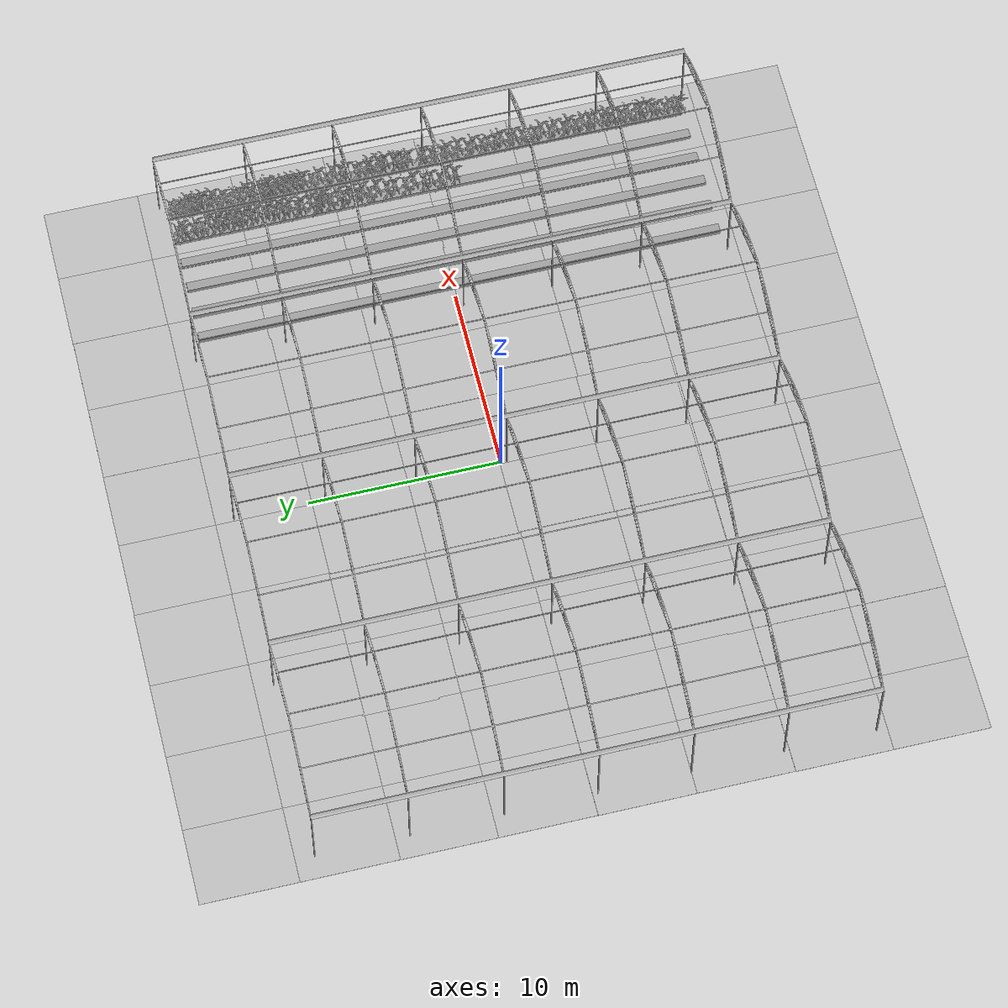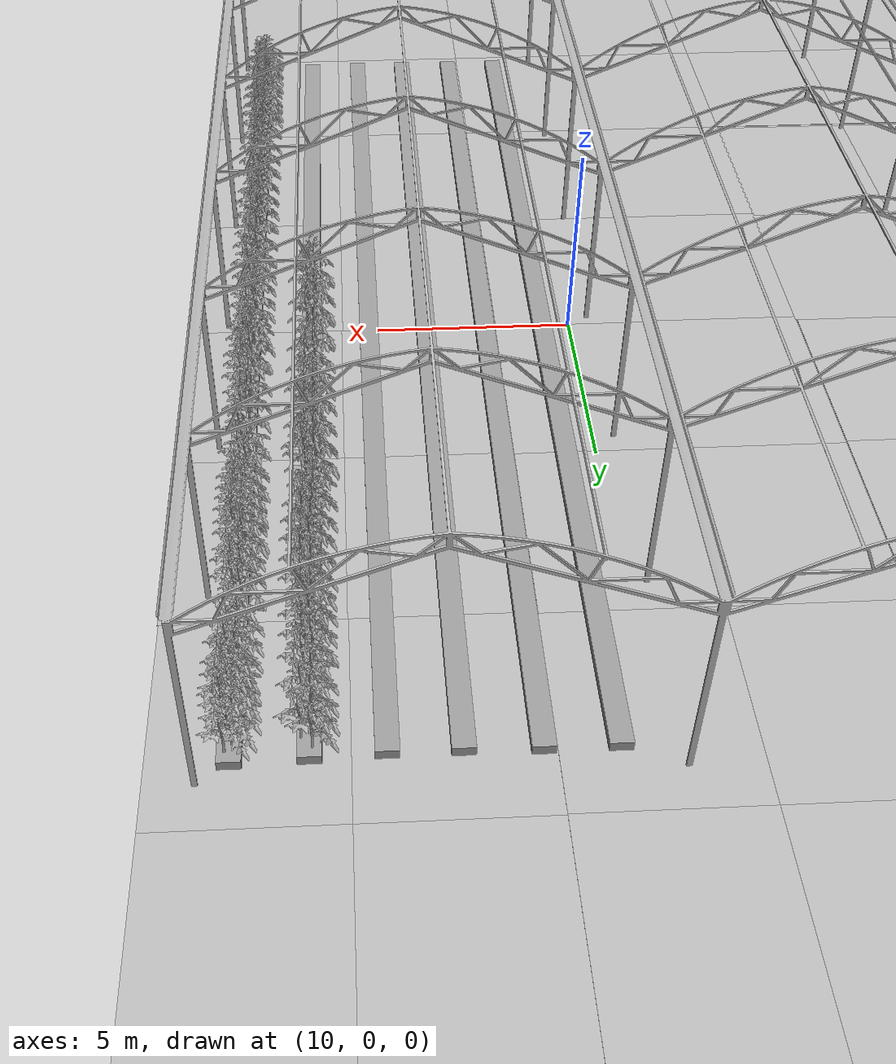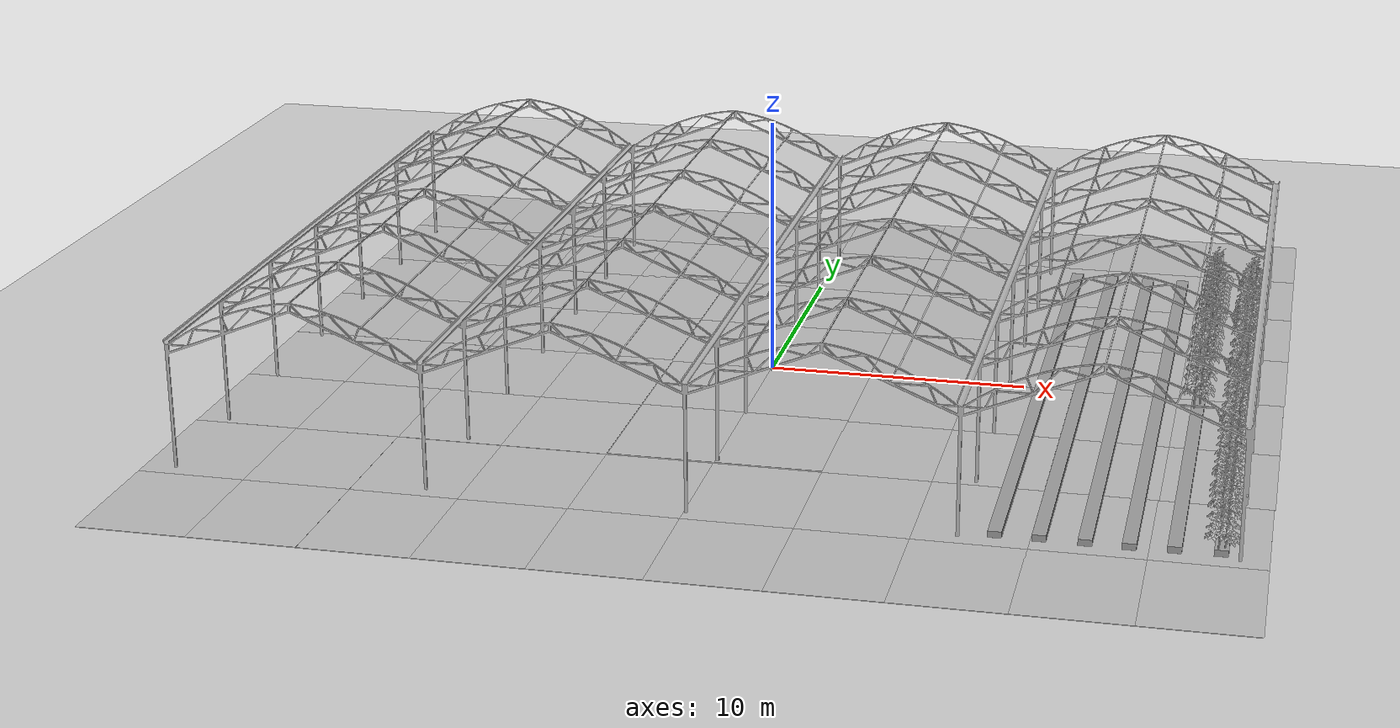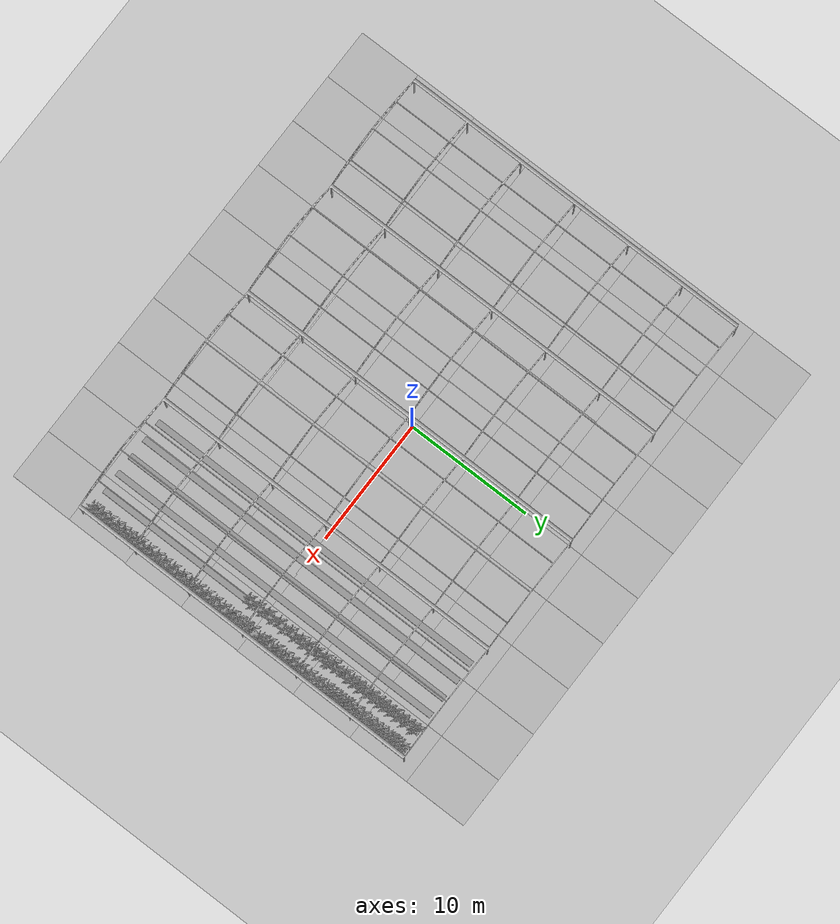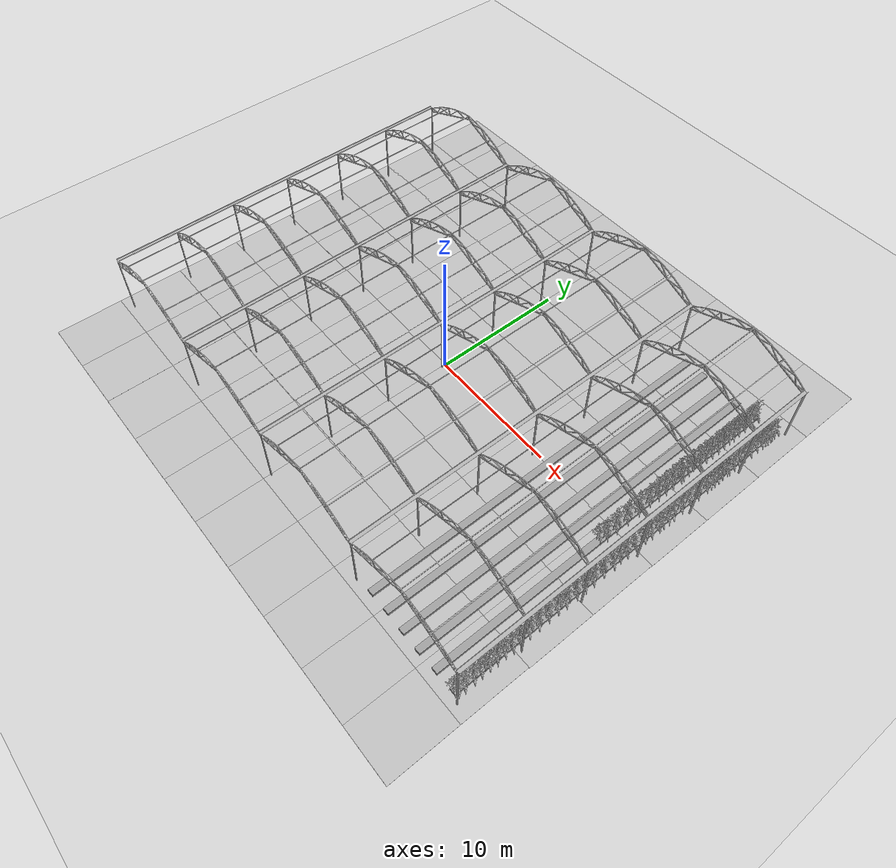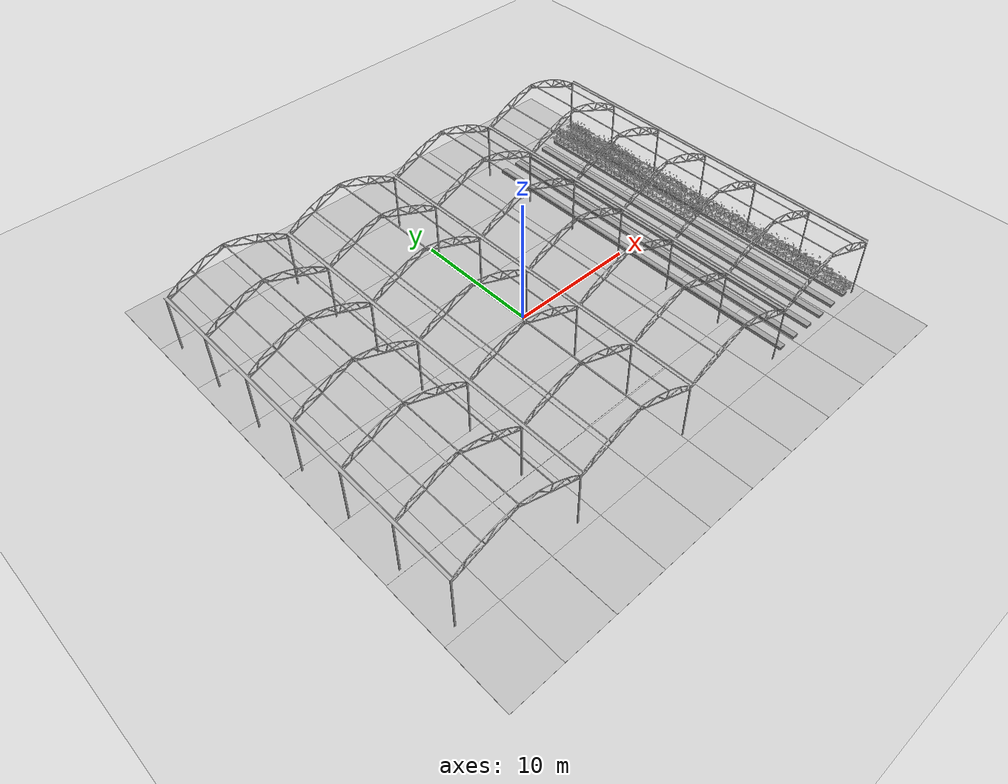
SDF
<sdf version="1.6">
 <world name="default">
  <light name="sun" type="directional">
   <pose>0 0 10 0 -0 0</pose>
   <diffuse>0.8 0.8 0.8 1</diffuse>
   <specular>0.2 0.2 0.2 1</specular>
   <attenuation>
    <range>1000</range>
    <constant>0.9</constant>
    <linear>0.01</linear>
    <quadratic>0.001</quadratic>
   </attenuation>
   <direction>-0.5 0.1 -0.9</direction>
  </light>
  <model name="ground_plane">
   <static>1</static>
   <link name="link">
    <collision name="collision">
     <geometry><plane><normal>0 0 1</normal><size>100 100</size></plane></geometry>
     <surface>
      <contact><collide_bitmask>65535</collide_bitmask></contact>
      <friction><ode><mu>100</mu><mu2>50</mu2></ode></friction>
     </surface>
    </collision>
    <visual name="visual">
     <cast_shadows>0</cast_shadows>
     <geometry><plane><normal>0 0 1</normal><size>100 100</size></plane></geometry>
     <material>
      <script><uri>file://media/materials/scripts/gazebo.material</uri><name>Gazebo/Grey</name></script>
     </material>
    </visual>
   </link>
  </model>
  <gravity>0 0 -9.8</gravity>
  <magnetic_field>6e-06 2.3e-05 -4.2e-05</magnetic_field>
  <atmosphere type="adiabatic"/>
  <physics name="default_physics" default="0" type="ode">
   <max_step_size>0.001</max_step_size>
   <real_time_factor>1</real_time_factor>
   <real_time_update_rate>1000</real_time_update_rate>
  </physics>
  <scene><ambient>0.4 0.4 0.4 1</ambient><background>0.7 0.7 0.7 1</background><shadows>1</shadows></scene>
  <audio><device>default</device></audio>
  <spherical_coordinates>
   <surface_model>EARTH_WGS84</surface_model>
   <latitude_deg>0</latitude_deg>
   <longitude_deg>0</longitude_deg>
   <elevation>0</elevation>
   <heading_deg>0</heading_deg>
  </spherical_coordinates>
  <model name="greenhouse">
   <static>1</static>
   <link name="link">
    <collision name="collision">
     <geometry>
      <mesh><scale>0.05 0.05 0.05</scale><uri>model://greenhouse/meshes/greenhouse.dae</uri></mesh>
     </geometry>
    </collision>
    <visual name="visual">
     <geometry>
      <mesh><scale>0.03 0.03 0.03</scale><uri>model://greenhouse/meshes/greenhouse.dae</uri></mesh>
     </geometry>
    </visual>
   </link>
   <pose>-24.6321 -23.8938 0 0 -0 0</pose>
  </model>
  <model name="mud_box_2">
   <static>1</static>
   <link name="link">
    <collision name="collision"><geometry><box><size>8 10 0.02</size></box></geometry></collision>
    <visual name="visual_1">
     <pose>-2 2.5 0 0 -0 0</pose>
     <cast_shadows>0</cast_shadows>
     <geometry><box><size>4 5 0.02</size></box></geometry>
     <material>
      <script>
       <uri>model://mud_box/materials/scripts</uri>
       <uri>model://mud_box/materials/textures</uri>
       <name>vrc/mud</name>
      </script>
     </material>
    </visual>
    <visual name="visual_2">
     <pose>2 2.5 0 0 -0 0</pose>
     <cast_shadows>0</cast_shadows>
     <geometry><box><size>4 5 0.02</size></box></geometry>
     <material>
      <script>
       <uri>model://mud_box/materials/scripts</uri>
       <uri>model://mud_box/materials/textures</uri>
       <name>vrc/mud</name>
      </script>
     </material>
    </visual>
    <visual name="visual_3">
     <pose>2 -2.5 0 0 -0 0</pose>
     <cast_shadows>0</cast_shadows>
     <geometry><box><size>4 5 0.02</size></box></geometry>
     <material>
      <script>
       <uri>model://mud_box/materials/scripts</uri>
       <uri>model://mud_box/materials/textures</uri>
       <name>vrc/mud</name>
      </script>
     </material>
    </visual>
    <visual name="visual_4">
     <pose>-2 -2.5 0 0 -0 0</pose>
     <cast_shadows>0</cast_shadows>
     <geometry><box><size>4 5 0.02</size></box></geometry>
     <material>
      <script>
       <uri>model://mud_box/materials/scripts</uri>
       <uri>model://mud_box/materials/textures</uri>
       <name>vrc/mud</name>
      </script>
     </material>
    </visual>
   </link>
   <pose>15.95 14.8768 0 0 -0 0</pose>
  </model>
  <model name="mud_box_2_clone">
   <static>1</static>
   <link name="link">
    <collision name="collision"><geometry><box><size>8 10 0.02</size></box></geometry></collision>
    <visual name="visual_1">
     <pose>-2 2.5 0 0 -0 0</pose>
     <cast_shadows>0</cast_shadows>
     <geometry><box><size>4 5 0.02</size></box></geometry>
     <material>
      <script>
       <uri>model://mud_box/materials/scripts</uri>
       <uri>model://mud_box/materials/textures</uri>
       <name>vrc/mud</name>
      </script>
     </material>
    </visual>
    <visual name="visual_2">
     <pose>2 2.5 0 0 -0 0</pose>
     <cast_shadows>0</cast_shadows>
     <geometry><box><size>4 5 0.02</size></box></geometry>
     <material>
      <script>
       <uri>model://mud_box/materials/scripts</uri>
       <uri>model://mud_box/materials/textures</uri>
       <name>vrc/mud</name>
      </script>
     </material>
    </visual>
    <visual name="visual_3">
     <pose>2 -2.5 0 0 -0 0</pose>
     <cast_shadows>0</cast_shadows>
     <geometry><box><size>4 5 0.02</size></box></geometry>
     <material>
      <script>
       <uri>model://mud_box/materials/scripts</uri>
       <uri>model://mud_box/materials/textures</uri>
       <name>vrc/mud</name>
      </script>
     </material>
    </visual>
    <visual name="visual_4">
     <pose>-2 -2.5 0 0 -0 0</pose>
     <cast_shadows>0</cast_shadows>
     <geometry><box><size>4 5 0.02</size></box></geometry>
     <material>
      <script>
       <uri>model://mud_box/materials/scripts</uri>
       <uri>model://mud_box/materials/textures</uri>
       <name>vrc/mud</name>
      </script>
     </material>
    </visual>
   </link>
   <pose>7.94862 14.8561 0 0 -0 0</pose>
  </model>
  <model name="mud_box_2_clone_0">
   <static>1</static>
   <link name="link">
    <collision name="collision"><geometry><box><size>8 10 0.02</size></box></geometry></collision>
    <visual name="visual_1">
     <pose>-2 2.5 0 0 -0 0</pose>
     <cast_shadows>0</cast_shadows>
     <geometry><box><size>4 5 0.02</size></box></geometry>
     <material>
      <script>
       <uri>model://mud_box/materials/scripts</uri>
       <uri>model://mud_box/materials/textures</uri>
       <name>vrc/mud</name>
      </script>
     </material>
    </visual>
    <visual name="visual_2">
     <pose>2 2.5 0 0 -0 0</pose>
     <cast_shadows>0</cast_shadows>
     <geometry><box><size>4 5 0.02</size></box></geometry>
     <material>
      <script>
       <uri>model://mud_box/materials/scripts</uri>
       <uri>model://mud_box/materials/textures</uri>
       <name>vrc/mud</name>
      </script>
     </material>
    </visual>
    <visual name="visual_3">
     <pose>2 -2.5 0 0 -0 0</pose>
     <cast_shadows>0</cast_shadows>
     <geometry><box><size>4 5 0.02</size></box></geometry>
     <material>
      <script>
       <uri>model://mud_box/materials/scripts</uri>
       <uri>model://mud_box/materials/textures</uri>
       <name>vrc/mud</name>
      </script>
     </material>
    </visual>
    <visual name="visual_4">
     <pose>-2 -2.5 0 0 -0 0</pose>
     <cast_shadows>0</cast_shadows>
     <geometry><box><size>4 5 0.02</size></box></geometry>
     <material>
      <script>
       <uri>model://mud_box/materials/scripts</uri>
       <uri>model://mud_box/materials/textures</uri>
       <name>vrc/mud</name>
      </script>
     </material>
    </visual>
   </link>
   <pose>-0.053733 14.862 0 0 -0 0</pose>
  </model>
  <model name="mud_box_2_clone_1">
   <static>1</static>
   <link name="link">
    <collision name="collision"><geometry><box><size>8 10 0.02</size></box></geometry></collision>
    <visual name="visual_1">
     <pose>-2 2.5 0 0 -0 0</pose>
     <cast_shadows>0</cast_shadows>
     <geometry><box><size>4 5 0.02</size></box></geometry>
     <material>
      <script>
       <uri>model://mud_box/materials/scripts</uri>
       <uri>model://mud_box/materials/textures</uri>
       <name>vrc/mud</name>
      </script>
     </material>
    </visual>
    <visual name="visual_2">
     <pose>2 2.5 0 0 -0 0</pose>
     <cast_shadows>0</cast_shadows>
     <geometry><box><size>4 5 0.02</size></box></geometry>
     <material>
      <script>
       <uri>model://mud_box/materials/scripts</uri>
       <uri>model://mud_box/materials/textures</uri>
       <name>vrc/mud</name>
      </script>
     </material>
    </visual>
    <visual name="visual_3">
     <pose>2 -2.5 0 0 -0 0</pose>
     <cast_shadows>0</cast_shadows>
     <geometry><box><size>4 5 0.02</size></box></geometry>
     <material>
      <script>
       <uri>model://mud_box/materials/scripts</uri>
       <uri>model://mud_box/materials/textures</uri>
       <name>vrc/mud</name>
      </script>
     </material>
    </visual>
    <visual name="visual_4">
     <pose>-2 -2.5 0 0 -0 0</pose>
     <cast_shadows>0</cast_shadows>
     <geometry><box><size>4 5 0.02</size></box></geometry>
     <material>
      <script>
       <uri>model://mud_box/materials/scripts</uri>
       <uri>model://mud_box/materials/textures</uri>
       <name>vrc/mud</name>
      </script>
     </material>
    </visual>
   </link>
   <pose>-8.0478 14.8839 0 0 -0 0</pose>
  </model>
  <model name="mud_box_2_clone_2">
   <static>1</static>
   <link name="link">
    <collision name="collision"><geometry><box><size>8 10 0.02</size></box></geometry></collision>
    <visual name="visual_1">
     <pose>-2 2.5 0 0 -0 0</pose>
     <cast_shadows>0</cast_shadows>
     <geometry><box><size>4 5 0.02</size></box></geometry>
     <material>
      <script>
       <uri>model://mud_box/materials/scripts</uri>
       <uri>model://mud_box/materials/textures</uri>
       <name>vrc/mud</name>
      </script>
     </material>
    </visual>
    <visual name="visual_2">
     <pose>2 2.5 0 0 -0 0</pose>
     <cast_shadows>0</cast_shadows>
     <geometry><box><size>4 5 0.02</size></box></geometry>
     <material>
      <script>
       <uri>model://mud_box/materials/scripts</uri>
       <uri>model://mud_box/materials/textures</uri>
       <name>vrc/mud</name>
      </script>
     </material>
    </visual>
    <visual name="visual_3">
     <pose>2 -2.5 0 0 -0 0</pose>
     <cast_shadows>0</cast_shadows>
     <geometry><box><size>4 5 0.02</size></box></geometry>
     <material>
      <script>
       <uri>model://mud_box/materials/scripts</uri>
       <uri>model://mud_box/materials/textures</uri>
       <name>vrc/mud</name>
      </script>
     </material>
    </visual>
    <visual name="visual_4">
     <pose>-2 -2.5 0 0 -0 0</pose>
     <cast_shadows>0</cast_shadows>
     <geometry><box><size>4 5 0.02</size></box></geometry>
     <material>
      <script>
       <uri>model://mud_box/materials/scripts</uri>
       <uri>model://mud_box/materials/textures</uri>
       <name>vrc/mud</name>
      </script>
     </material>
    </visual>
   </link>
   <pose>-16.0172 14.8764 0 0 -0 0</pose>
  </model>
  <model name="mud_box_2_clone_3">
   <static>1</static>
   <link name="link">
    <collision name="collision"><geometry><box><size>8 10 0.02</size></box></geometry></collision>
    <visual name="visual_1">
     <pose>-2 2.5 0 0 -0 0</pose>
     <cast_shadows>0</cast_shadows>
     <geometry><box><size>4 5 0.02</size></box></geometry>
     <material>
      <script>
       <uri>model://mud_box/materials/scripts</uri>
       <uri>model://mud_box/materials/textures</uri>
       <name>vrc/mud</name>
      </script>
     </material>
    </visual>
    <visual name="visual_2">
     <pose>2 2.5 0 0 -0 0</pose>
     <cast_shadows>0</cast_shadows>
     <geometry><box><size>4 5 0.02</size></box></geometry>
     <material>
      <script>
       <uri>model://mud_box/materials/scripts</uri>
       <uri>model://mud_box/materials/textures</uri>
       <name>vrc/mud</name>
      </script>
     </material>
    </visual>
    <visual name="visual_3">
     <pose>2 -2.5 0 0 -0 0</pose>
     <cast_shadows>0</cast_shadows>
     <geometry><box><size>4 5 0.02</size></box></geometry>
     <material>
      <script>
       <uri>model://mud_box/materials/scripts</uri>
       <uri>model://mud_box/materials/textures</uri>
       <name>vrc/mud</name>
      </script>
     </material>
    </visual>
    <visual name="visual_4">
     <pose>-2 -2.5 0 0 -0 0</pose>
     <cast_shadows>0</cast_shadows>
     <geometry><box><size>4 5 0.02</size></box></geometry>
     <material>
      <script>
       <uri>model://mud_box/materials/scripts</uri>
       <uri>model://mud_box/materials/textures</uri>
       <name>vrc/mud</name>
      </script>
     </material>
    </visual>
   </link>
   <pose>15.9717 4.88727 0 0 -0 0</pose>
  </model>
  <model name="mud_box_2_clone_4">
   <static>1</static>
   <link name="link">
    <collision name="collision"><geometry><box><size>8 10 0.02</size></box></geometry></collision>
    <visual name="visual_1">
     <pose>-2 2.5 0 0 -0 0</pose>
     <cast_shadows>0</cast_shadows>
     <geometry><box><size>4 5 0.02</size></box></geometry>
     <material>
      <script>
       <uri>model://mud_box/materials/scripts</uri>
       <uri>model://mud_box/materials/textures</uri>
       <name>vrc/mud</name>
      </script>
     </material>
    </visual>
    <visual name="visual_2">
     <pose>2 2.5 0 0 -0 0</pose>
     <cast_shadows>0</cast_shadows>
     <geometry><box><size>4 5 0.02</size></box></geometry>
     <material>
      <script>
       <uri>model://mud_box/materials/scripts</uri>
       <uri>model://mud_box/materials/textures</uri>
       <name>vrc/mud</name>
      </script>
     </material>
    </visual>
    <visual name="visual_3">
     <pose>2 -2.5 0 0 -0 0</pose>
     <cast_shadows>0</cast_shadows>
     <geometry><box><size>4 5 0.02</size></box></geometry>
     <material>
      <script>
       <uri>model://mud_box/materials/scripts</uri>
       <uri>model://mud_box/materials/textures</uri>
       <name>vrc/mud</name>
      </script>
     </material>
    </visual>
    <visual name="visual_4">
     <pose>-2 -2.5 0 0 -0 0</pose>
     <cast_shadows>0</cast_shadows>
     <geometry><box><size>4 5 0.02</size></box></geometry>
     <material>
      <script>
       <uri>model://mud_box/materials/scripts</uri>
       <uri>model://mud_box/materials/textures</uri>
       <name>vrc/mud</name>
      </script>
     </material>
    </visual>
   </link>
   <pose>15.9437 -5.04402 0 0 -0 0</pose>
  </model>
  <model name="mud_box_2_clone_5">
   <static>1</static>
   <link name="link">
    <collision name="collision"><geometry><box><size>8 10 0.02</size></box></geometry></collision>
    <visual name="visual_1">
     <pose>-2 2.5 0 0 -0 0</pose>
     <cast_shadows>0</cast_shadows>
     <geometry><box><size>4 5 0.02</size></box></geometry>
     <material>
      <script>
       <uri>model://mud_box/materials/scripts</uri>
       <uri>model://mud_box/materials/textures</uri>
       <name>vrc/mud</name>
      </script>
     </material>
    </visual>
    <visual name="visual_2">
     <pose>2 2.5 0 0 -0 0</pose>
     <cast_shadows>0</cast_shadows>
     <geometry><box><size>4 5 0.02</size></box></geometry>
     <material>
      <script>
       <uri>model://mud_box/materials/scripts</uri>
       <uri>model://mud_box/materials/textures</uri>
       <name>vrc/mud</name>
      </script>
     </material>
    </visual>
    <visual name="visual_3">
     <pose>2 -2.5 0 0 -0 0</pose>
     <cast_shadows>0</cast_shadows>
     <geometry><box><size>4 5 0.02</size></box></geometry>
     <material>
      <script>
       <uri>model://mud_box/materials/scripts</uri>
       <uri>model://mud_box/materials/textures</uri>
       <name>vrc/mud</name>
      </script>
     </material>
    </visual>
    <visual name="visual_4">
     <pose>-2 -2.5 0 0 -0 0</pose>
     <cast_shadows>0</cast_shadows>
     <geometry><box><size>4 5 0.02</size></box></geometry>
     <material>
      <script>
       <uri>model://mud_box/materials/scripts</uri>
       <uri>model://mud_box/materials/textures</uri>
       <name>vrc/mud</name>
      </script>
     </material>
    </visual>
   </link>
   <pose>15.9026 -15.0305 0 0 -0 0</pose>
  </model>
  <model name="mud_box_2_clone_6">
   <static>1</static>
   <link name="link">
    <collision name="collision"><geometry><box><size>8 10 0.02</size></box></geometry></collision>
    <visual name="visual_1">
     <pose>-2 2.5 0 0 -0 0</pose>
     <cast_shadows>0</cast_shadows>
     <geometry><box><size>4 5 0.02</size></box></geometry>
     <material>
      <script>
       <uri>model://mud_box/materials/scripts</uri>
       <uri>model://mud_box/materials/textures</uri>
       <name>vrc/mud</name>
      </script>
     </material>
    </visual>
    <visual name="visual_2">
     <pose>2 2.5 0 0 -0 0</pose>
     <cast_shadows>0</cast_shadows>
     <geometry><box><size>4 5 0.02</size></box></geometry>
     <material>
      <script>
       <uri>model://mud_box/materials/scripts</uri>
       <uri>model://mud_box/materials/textures</uri>
       <name>vrc/mud</name>
      </script>
     </material>
    </visual>
    <visual name="visual_3">
     <pose>2 -2.5 0 0 -0 0</pose>
     <cast_shadows>0</cast_shadows>
     <geometry><box><size>4 5 0.02</size></box></geometry>
     <material>
      <script>
       <uri>model://mud_box/materials/scripts</uri>
       <uri>model://mud_box/materials/textures</uri>
       <name>vrc/mud</name>
      </script>
     </material>
    </visual>
    <visual name="visual_4">
     <pose>-2 -2.5 0 0 -0 0</pose>
     <cast_shadows>0</cast_shadows>
     <geometry><box><size>4 5 0.02</size></box></geometry>
     <material>
      <script>
       <uri>model://mud_box/materials/scripts</uri>
       <uri>model://mud_box/materials/textures</uri>
       <name>vrc/mud</name>
      </script>
     </material>
    </visual>
   </link>
   <pose>7.92837 -15.034 0 0 -0 0</pose>
  </model>
  <model name="mud_box_2_clone_7">
   <static>1</static>
   <link name="link">
    <collision name="collision"><geometry><box><size>8 10 0.02</size></box></geometry></collision>
    <visual name="visual_1">
     <pose>-2 2.5 0 0 -0 0</pose>
     <cast_shadows>0</cast_shadows>
     <geometry><box><size>4 5 0.02</size></box></geometry>
     <material>
      <script>
       <uri>model://mud_box/materials/scripts</uri>
       <uri>model://mud_box/materials/textures</uri>
       <name>vrc/mud</name>
      </script>
     </material>
    </visual>
    <visual name="visual_2">
     <pose>2 2.5 0 0 -0 0</pose>
     <cast_shadows>0</cast_shadows>
     <geometry><box><size>4 5 0.02</size></box></geometry>
     <material>
      <script>
       <uri>model://mud_box/materials/scripts</uri>
       <uri>model://mud_box/materials/textures</uri>
       <name>vrc/mud</name>
      </script>
     </material>
    </visual>
    <visual name="visual_3">
     <pose>2 -2.5 0 0 -0 0</pose>
     <cast_shadows>0</cast_shadows>
     <geometry><box><size>4 5 0.02</size></box></geometry>
     <material>
      <script>
       <uri>model://mud_box/materials/scripts</uri>
       <uri>model://mud_box/materials/textures</uri>
       <name>vrc/mud</name>
      </script>
     </material>
    </visual>
    <visual name="visual_4">
     <pose>-2 -2.5 0 0 -0 0</pose>
     <cast_shadows>0</cast_shadows>
     <geometry><box><size>4 5 0.02</size></box></geometry>
     <material>
      <script>
       <uri>model://mud_box/materials/scripts</uri>
       <uri>model://mud_box/materials/textures</uri>
       <name>vrc/mud</name>
      </script>
     </material>
    </visual>
   </link>
   <pose>-0.060925 -15.032 0 0 -0 0</pose>
  </model>
  <model name="mud_box_2_clone_8">
   <static>1</static>
   <link name="link">
    <collision name="collision"><geometry><box><size>8 10 0.02</size></box></geometry></collision>
    <visual name="visual_1">
     <pose>-2 2.5 0 0 -0 0</pose>
     <cast_shadows>0</cast_shadows>
     <geometry><box><size>4 5 0.02</size></box></geometry>
     <material>
      <script>
       <uri>model://mud_box/materials/scripts</uri>
       <uri>model://mud_box/materials/textures</uri>
       <name>vrc/mud</name>
      </script>
     </material>
    </visual>
    <visual name="visual_2">
     <pose>2 2.5 0 0 -0 0</pose>
     <cast_shadows>0</cast_shadows>
     <geometry><box><size>4 5 0.02</size></box></geometry>
     <material>
      <script>
       <uri>model://mud_box/materials/scripts</uri>
       <uri>model://mud_box/materials/textures</uri>
       <name>vrc/mud</name>
      </script>
     </material>
    </visual>
    <visual name="visual_3">
     <pose>2 -2.5 0 0 -0 0</pose>
     <cast_shadows>0</cast_shadows>
     <geometry><box><size>4 5 0.02</size></box></geometry>
     <material>
      <script>
       <uri>model://mud_box/materials/scripts</uri>
       <uri>model://mud_box/materials/textures</uri>
       <name>vrc/mud</name>
      </script>
     </material>
    </visual>
    <visual name="visual_4">
     <pose>-2 -2.5 0 0 -0 0</pose>
     <cast_shadows>0</cast_shadows>
     <geometry><box><size>4 5 0.02</size></box></geometry>
     <material>
      <script>
       <uri>model://mud_box/materials/scripts</uri>
       <uri>model://mud_box/materials/textures</uri>
       <name>vrc/mud</name>
      </script>
     </material>
    </visual>
   </link>
   <pose>-8.05527 -15.0417 0 0 -0 0</pose>
  </model>
  <model name="mud_box_2_clone_9">
   <static>1</static>
   <link name="link">
    <collision name="collision"><geometry><box><size>8 10 0.02</size></box></geometry></collision>
    <visual name="visual_1">
     <pose>-2 2.5 0 0 -0 0</pose>
     <cast_shadows>0</cast_shadows>
     <geometry><box><size>4 5 0.02</size></box></geometry>
     <material>
      <script>
       <uri>model://mud_box/materials/scripts</uri>
       <uri>model://mud_box/materials/textures</uri>
       <name>vrc/mud</name>
      </script>
     </material>
    </visual>
    <visual name="visual_2">
     <pose>2 2.5 0 0 -0 0</pose>
     <cast_shadows>0</cast_shadows>
     <geometry><box><size>4 5 0.02</size></box></geometry>
     <material>
      <script>
       <uri>model://mud_box/materials/scripts</uri>
       <uri>model://mud_box/materials/textures</uri>
       <name>vrc/mud</name>
      </script>
     </material>
    </visual>
    <visual name="visual_3">
     <pose>2 -2.5 0 0 -0 0</pose>
     <cast_shadows>0</cast_shadows>
     <geometry><box><size>4 5 0.02</size></box></geometry>
     <material>
      <script>
       <uri>model://mud_box/materials/scripts</uri>
       <uri>model://mud_box/materials/textures</uri>
       <name>vrc/mud</name>
      </script>
     </material>
    </visual>
    <visual name="visual_4">
     <pose>-2 -2.5 0 0 -0 0</pose>
     <cast_shadows>0</cast_shadows>
     <geometry><box><size>4 5 0.02</size></box></geometry>
     <material>
      <script>
       <uri>model://mud_box/materials/scripts</uri>
       <uri>model://mud_box/materials/textures</uri>
       <name>vrc/mud</name>
      </script>
     </material>
    </visual>
   </link>
   <pose>-16.0602 -15.033 0 0 -0 0</pose>
  </model>
  <model name="mud_box_2_clone_10">
   <static>1</static>
   <link name="link">
    <collision name="collision"><geometry><box><size>8 10 0.02</size></box></geometry></collision>
    <visual name="visual_1">
     <pose>-2 2.5 0 0 -0 0</pose>
     <cast_shadows>0</cast_shadows>
     <geometry><box><size>4 5 0.02</size></box></geometry>
     <material>
      <script>
       <uri>model://mud_box/materials/scripts</uri>
       <uri>model://mud_box/materials/textures</uri>
       <name>vrc/mud</name>
      </script>
     </material>
    </visual>
    <visual name="visual_2">
     <pose>2 2.5 0 0 -0 0</pose>
     <cast_shadows>0</cast_shadows>
     <geometry><box><size>4 5 0.02</size></box></geometry>
     <material>
      <script>
       <uri>model://mud_box/materials/scripts</uri>
       <uri>model://mud_box/materials/textures</uri>
       <name>vrc/mud</name>
      </script>
     </material>
    </visual>
    <visual name="visual_3">
     <pose>2 -2.5 0 0 -0 0</pose>
     <cast_shadows>0</cast_shadows>
     <geometry><box><size>4 5 0.02</size></box></geometry>
     <material>
      <script>
       <uri>model://mud_box/materials/scripts</uri>
       <uri>model://mud_box/materials/textures</uri>
       <name>vrc/mud</name>
      </script>
     </material>
    </visual>
    <visual name="visual_4">
     <pose>-2 -2.5 0 0 -0 0</pose>
     <cast_shadows>0</cast_shadows>
     <geometry><box><size>4 5 0.02</size></box></geometry>
     <material>
      <script>
       <uri>model://mud_box/materials/scripts</uri>
       <uri>model://mud_box/materials/textures</uri>
       <name>vrc/mud</name>
      </script>
     </material>
    </visual>
   </link>
   <pose>-16.037 -5.02979 0 0 -0 0</pose>
  </model>
  <model name="mud_box_2_clone_11">
   <static>1</static>
   <link name="link">
    <collision name="collision"><geometry><box><size>8 10 0.02</size></box></geometry></collision>
    <visual name="visual_1">
     <pose>-2 2.5 0 0 -0 0</pose>
     <cast_shadows>0</cast_shadows>
     <geometry><box><size>4 5 0.02</size></box></geometry>
     <material>
      <script>
       <uri>model://mud_box/materials/scripts</uri>
       <uri>model://mud_box/materials/textures</uri>
       <name>vrc/mud</name>
      </script>
     </material>
    </visual>
    <visual name="visual_2">
     <pose>2 2.5 0 0 -0 0</pose>
     <cast_shadows>0</cast_shadows>
     <geometry><box><size>4 5 0.02</size></box></geometry>
     <material>
      <script>
       <uri>model://mud_box/materials/scripts</uri>
       <uri>model://mud_box/materials/textures</uri>
       <name>vrc/mud</name>
      </script>
     </material>
    </visual>
    <visual name="visual_3">
     <pose>2 -2.5 0 0 -0 0</pose>
     <cast_shadows>0</cast_shadows>
     <geometry><box><size>4 5 0.02</size></box></geometry>
     <material>
      <script>
       <uri>model://mud_box/materials/scripts</uri>
       <uri>model://mud_box/materials/textures</uri>
       <name>vrc/mud</name>
      </script>
     </material>
    </visual>
    <visual name="visual_4">
     <pose>-2 -2.5 0 0 -0 0</pose>
     <cast_shadows>0</cast_shadows>
     <geometry><box><size>4 5 0.02</size></box></geometry>
     <material>
      <script>
       <uri>model://mud_box/materials/scripts</uri>
       <uri>model://mud_box/materials/textures</uri>
       <name>vrc/mud</name>
      </script>
     </material>
    </visual>
   </link>
   <pose>-16.0272 4.97532 0 0 -0 0</pose>
  </model>
  <model name="mud_box_2_clone_12">
   <static>1</static>
   <link name="link">
    <collision name="collision"><geometry><box><size>8 10 0.02</size></box></geometry></collision>
    <visual name="visual_1">
     <pose>-2 2.5 0 0 -0 0</pose>
     <cast_shadows>0</cast_shadows>
     <geometry><box><size>4 5 0.02</size></box></geometry>
     <material>
      <script>
       <uri>model://mud_box/materials/scripts</uri>
       <uri>model://mud_box/materials/textures</uri>
       <name>vrc/mud</name>
      </script>
     </material>
    </visual>
    <visual name="visual_2">
     <pose>2 2.5 0 0 -0 0</pose>
     <cast_shadows>0</cast_shadows>
     <geometry><box><size>4 5 0.02</size></box></geometry>
     <material>
      <script>
       <uri>model://mud_box/materials/scripts</uri>
       <uri>model://mud_box/materials/textures</uri>
       <name>vrc/mud</name>
      </script>
     </material>
    </visual>
    <visual name="visual_3">
     <pose>2 -2.5 0 0 -0 0</pose>
     <cast_shadows>0</cast_shadows>
     <geometry><box><size>4 5 0.02</size></box></geometry>
     <material>
      <script>
       <uri>model://mud_box/materials/scripts</uri>
       <uri>model://mud_box/materials/textures</uri>
       <name>vrc/mud</name>
      </script>
     </material>
    </visual>
    <visual name="visual_4">
     <pose>-2 -2.5 0 0 -0 0</pose>
     <cast_shadows>0</cast_shadows>
     <geometry><box><size>4 5 0.02</size></box></geometry>
     <material>
      <script>
       <uri>model://mud_box/materials/scripts</uri>
       <uri>model://mud_box/materials/textures</uri>
       <name>vrc/mud</name>
      </script>
     </material>
    </visual>
   </link>
   <pose>-8.1226 4.98139 0 0 -0 0</pose>
  </model>
  <model name="mud_box_2_clone_13">
   <static>1</static>
   <link name="link">
    <collision name="collision"><geometry><box><size>8 10 0.02</size></box></geometry></collision>
    <visual name="visual_1">
     <pose>-2 2.5 0 0 -0 0</pose>
     <cast_shadows>0</cast_shadows>
     <geometry><box><size>4 5 0.02</size></box></geometry>
     <material>
      <script>
       <uri>model://mud_box/materials/scripts</uri>
       <uri>model://mud_box/materials/textures</uri>
       <name>vrc/mud</name>
      </script>
     </material>
    </visual>
    <visual name="visual_2">
     <pose>2 2.5 0 0 -0 0</pose>
     <cast_shadows>0</cast_shadows>
     <geometry><box><size>4 5 0.02</size></box></geometry>
     <material>
      <script>
       <uri>model://mud_box/materials/scripts</uri>
       <uri>model://mud_box/materials/textures</uri>
       <name>vrc/mud</name>
      </script>
     </material>
    </visual>
    <visual name="visual_3">
     <pose>2 -2.5 0 0 -0 0</pose>
     <cast_shadows>0</cast_shadows>
     <geometry><box><size>4 5 0.02</size></box></geometry>
     <material>
      <script>
       <uri>model://mud_box/materials/scripts</uri>
       <uri>model://mud_box/materials/textures</uri>
       <name>vrc/mud</name>
      </script>
     </material>
    </visual>
    <visual name="visual_4">
     <pose>-2 -2.5 0 0 -0 0</pose>
     <cast_shadows>0</cast_shadows>
     <geometry><box><size>4 5 0.02</size></box></geometry>
     <material>
      <script>
       <uri>model://mud_box/materials/scripts</uri>
       <uri>model://mud_box/materials/textures</uri>
       <name>vrc/mud</name>
      </script>
     </material>
    </visual>
   </link>
   <pose>-8.07337 -5.01851 0 0 -0 0</pose>
  </model>
  <model name="mud_box_2_clone_14">
   <static>1</static>
   <link name="link">
    <collision name="collision"><geometry><box><size>8 10 0.02</size></box></geometry></collision>
    <visual name="visual_1">
     <pose>-2 2.5 0 0 -0 0</pose>
     <cast_shadows>0</cast_shadows>
     <geometry><box><size>4 5 0.02</size></box></geometry>
     <material>
      <script>
       <uri>model://mud_box/materials/scripts</uri>
       <uri>model://mud_box/materials/textures</uri>
       <name>vrc/mud</name>
      </script>
     </material>
    </visual>
    <visual name="visual_2">
     <pose>2 2.5 0 0 -0 0</pose>
     <cast_shadows>0</cast_shadows>
     <geometry><box><size>4 5 0.02</size></box></geometry>
     <material>
      <script>
       <uri>model://mud_box/materials/scripts</uri>
       <uri>model://mud_box/materials/textures</uri>
       <name>vrc/mud</name>
      </script>
     </material>
    </visual>
    <visual name="visual_3">
     <pose>2 -2.5 0 0 -0 0</pose>
     <cast_shadows>0</cast_shadows>
     <geometry><box><size>4 5 0.02</size></box></geometry>
     <material>
      <script>
       <uri>model://mud_box/materials/scripts</uri>
       <uri>model://mud_box/materials/textures</uri>
       <name>vrc/mud</name>
      </script>
     </material>
    </visual>
    <visual name="visual_4">
     <pose>-2 -2.5 0 0 -0 0</pose>
     <cast_shadows>0</cast_shadows>
     <geometry><box><size>4 5 0.02</size></box></geometry>
     <material>
      <script>
       <uri>model://mud_box/materials/scripts</uri>
       <uri>model://mud_box/materials/textures</uri>
       <name>vrc/mud</name>
      </script>
     </material>
    </visual>
   </link>
   <pose>7.92131 -5.03606 0 0 -0 0</pose>
  </model>
  <model name="mud_box_2_clone_15">
   <static>1</static>
   <link name="link">
    <collision name="collision"><geometry><box><size>8 10 0.02</size></box></geometry></collision>
    <visual name="visual_1">
     <pose>-2 2.5 0 0 -0 0</pose>
     <cast_shadows>0</cast_shadows>
     <geometry><box><size>4 5 0.02</size></box></geometry>
     <material>
      <script>
       <uri>model://mud_box/materials/scripts</uri>
       <uri>model://mud_box/materials/textures</uri>
       <name>vrc/mud</name>
      </script>
     </material>
    </visual>
    <visual name="visual_2">
     <pose>2 2.5 0 0 -0 0</pose>
     <cast_shadows>0</cast_shadows>
     <geometry><box><size>4 5 0.02</size></box></geometry>
     <material>
      <script>
       <uri>model://mud_box/materials/scripts</uri>
       <uri>model://mud_box/materials/textures</uri>
       <name>vrc/mud</name>
      </script>
     </material>
    </visual>
    <visual name="visual_3">
     <pose>2 -2.5 0 0 -0 0</pose>
     <cast_shadows>0</cast_shadows>
     <geometry><box><size>4 5 0.02</size></box></geometry>
     <material>
      <script>
       <uri>model://mud_box/materials/scripts</uri>
       <uri>model://mud_box/materials/textures</uri>
       <name>vrc/mud</name>
      </script>
     </material>
    </visual>
    <visual name="visual_4">
     <pose>-2 -2.5 0 0 -0 0</pose>
     <cast_shadows>0</cast_shadows>
     <geometry><box><size>4 5 0.02</size></box></geometry>
     <material>
      <script>
       <uri>model://mud_box/materials/scripts</uri>
       <uri>model://mud_box/materials/textures</uri>
       <name>vrc/mud</name>
      </script>
     </material>
    </visual>
   </link>
   <pose>-0.044632 -4.93319 0 0 -0 0</pose>
  </model>
  <model name="mud_box_2_clone_16">
   <static>1</static>
   <link name="link">
    <collision name="collision"><geometry><box><size>8 10 0.02</size></box></geometry></collision>
    <visual name="visual_1">
     <pose>-2 2.5 0 0 -0 0</pose>
     <cast_shadows>0</cast_shadows>
     <geometry><box><size>4 5 0.02</size></box></geometry>
     <material>
      <script>
       <uri>model://mud_box/materials/scripts</uri>
       <uri>model://mud_box/materials/textures</uri>
       <name>vrc/mud</name>
      </script>
     </material>
    </visual>
    <visual name="visual_2">
     <pose>2 2.5 0 0 -0 0</pose>
     <cast_shadows>0</cast_shadows>
     <geometry><box><size>4 5 0.02</size></box></geometry>
     <material>
      <script>
       <uri>model://mud_box/materials/scripts</uri>
       <uri>model://mud_box/materials/textures</uri>
       <name>vrc/mud</name>
      </script>
     </material>
    </visual>
    <visual name="visual_3">
     <pose>2 -2.5 0 0 -0 0</pose>
     <cast_shadows>0</cast_shadows>
     <geometry><box><size>4 5 0.02</size></box></geometry>
     <material>
      <script>
       <uri>model://mud_box/materials/scripts</uri>
       <uri>model://mud_box/materials/textures</uri>
       <name>vrc/mud</name>
      </script>
     </material>
    </visual>
    <visual name="visual_4">
     <pose>-2 -2.5 0 0 -0 0</pose>
     <cast_shadows>0</cast_shadows>
     <geometry><box><size>4 5 0.02</size></box></geometry>
     <material>
      <script>
       <uri>model://mud_box/materials/scripts</uri>
       <uri>model://mud_box/materials/textures</uri>
       <name>vrc/mud</name>
      </script>
     </material>
    </visual>
   </link>
   <pose>7.93489 4.92736 0 0 -0 0</pose>
  </model>
  <model name="mud_box_2_clone_17">
   <static>1</static>
   <link name="link">
    <collision name="collision"><geometry><box><size>8 10 0.02</size></box></geometry></collision>
    <visual name="visual_1">
     <pose>-2 2.5 0 0 -0 0</pose>
     <cast_shadows>0</cast_shadows>
     <geometry><box><size>4 5 0.02</size></box></geometry>
     <material>
      <script>
       <uri>model://mud_box/materials/scripts</uri>
       <uri>model://mud_box/materials/textures</uri>
       <name>vrc/mud</name>
      </script>
     </material>
    </visual>
    <visual name="visual_2">
     <pose>2 2.5 0 0 -0 0</pose>
     <cast_shadows>0</cast_shadows>
     <geometry><box><size>4 5 0.02</size></box></geometry>
     <material>
      <script>
       <uri>model://mud_box/materials/scripts</uri>
       <uri>model://mud_box/materials/textures</uri>
       <name>vrc/mud</name>
      </script>
     </material>
    </visual>
    <visual name="visual_3">
     <pose>2 -2.5 0 0 -0 0</pose>
     <cast_shadows>0</cast_shadows>
     <geometry><box><size>4 5 0.02</size></box></geometry>
     <material>
      <script>
       <uri>model://mud_box/materials/scripts</uri>
       <uri>model://mud_box/materials/textures</uri>
       <name>vrc/mud</name>
      </script>
     </material>
    </visual>
    <visual name="visual_4">
     <pose>-2 -2.5 0 0 -0 0</pose>
     <cast_shadows>0</cast_shadows>
     <geometry><box><size>4 5 0.02</size></box></geometry>
     <material>
      <script>
       <uri>model://mud_box/materials/scripts</uri>
       <uri>model://mud_box/materials/textures</uri>
       <name>vrc/mud</name>
      </script>
     </material>
    </visual>
   </link>
   <pose>-0.092613 4.86457 0 0 -0 0</pose>
  </model>
  <model name="plant_base_clone_clone_0_clone">
   <link name="link">
    <inertial>
     <mass>1</mass>
     <inertia>
      <ixx>0.166667</ixx>
      <ixy>0</ixy>
      <ixz>0</ixz>
      <iyy>0.166667</iyy>
      <iyz>0</iyz>
      <izz>0.166667</izz>
     </inertia>
    </inertial>
    <visual name="visual">
     <geometry><box><size>0.484753 27.8593 0.235695</size></box></geometry>
     <material>
      <script><name>Gazebo/Grey</name><uri>file://media/materials/scripts/gazebo.material</uri></script>
     </material>
    </visual>
    <collision name="collision">
     <geometry><box><size>0.484753 27.8593 0.235695</size></box></geometry>
     <surface>
      <friction>
       <ode><mu>1</mu><mu2>1</mu2><fdir1>0 0 0</fdir1><slip1>0</slip1><slip2>0</slip2></ode>
       <torsional>
        <coefficient>1</coefficient>
        <patch_radius>0</patch_radius>
        <surface_radius>0</surface_radius>
        <use_patch_radius>1</use_patch_radius>
        <ode><slip>0</slip></ode>
       </torsional>
      </friction>
      <bounce><restitution_coefficient>0</restitution_coefficient><threshold>1e+06</threshold></bounce>
      <contact>
       <collide_without_contact>0</collide_without_contact>
       <collide_without_contact_bitmask>1</collide_without_contact_bitmask>
       <collide_bitmask>1</collide_bitmask>
       <ode>
        <soft_cfm>0</soft_cfm>
        <soft_erp>0.2</soft_erp>
        <kp>1e+13</kp>
        <kd>1</kd>
        <max_vel>0.01</max_vel>
        <min_depth>0</min_depth>
       </ode>
       <bullet>
        <split_impulse>1</split_impulse>
        <split_impulse_penetration_threshold>-0.01</split_impulse_penetration_threshold>
        <soft_cfm>0</soft_cfm>
        <soft_erp>0.2</soft_erp>
        <kp>1e+13</kp>
        <kd>1</kd>
       </bullet>
      </contact>
     </surface>
    </collision>
   </link>
   <static>1</static>
   <pose>16.7542 -0.411562 0.134309 0 -0 0</pose>
  </model>
  <model name="plant_base_clone_clone_0_clone_0">
   <link name="link">
    <inertial>
     <mass>1</mass>
     <inertia>
      <ixx>0.166667</ixx>
      <ixy>0</ixy>
      <ixz>0</ixz>
      <iyy>0.166667</iyy>
      <iyz>0</iyz>
      <izz>0.166667</izz>
     </inertia>
    </inertial>
    <visual name="visual">
     <geometry><box><size>0.484753 27.8593 0.235695</size></box></geometry>
     <material>
      <script><name>Gazebo/Grey</name><uri>file://media/materials/scripts/gazebo.material</uri></script>
     </material>
    </visual>
    <collision name="collision">
     <geometry><box><size>0.484753 27.8593 0.235695</size></box></geometry>
     <surface>
      <friction>
       <ode><mu>1</mu><mu2>1</mu2><fdir1>0 0 0</fdir1><slip1>0</slip1><slip2>0</slip2></ode>
       <torsional>
        <coefficient>1</coefficient>
        <patch_radius>0</patch_radius>
        <surface_radius>0</surface_radius>
        <use_patch_radius>1</use_patch_radius>
        <ode><slip>0</slip></ode>
       </torsional>
      </friction>
      <bounce><restitution_coefficient>0</restitution_coefficient><threshold>1e+06</threshold></bounce>
      <contact>
       <collide_without_contact>0</collide_without_contact>
       <collide_without_contact_bitmask>1</collide_without_contact_bitmask>
       <collide_bitmask>1</collide_bitmask>
       <ode>
        <soft_cfm>0</soft_cfm>
        <soft_erp>0.2</soft_erp>
        <kp>1e+13</kp>
        <kd>1</kd>
        <max_vel>0.01</max_vel>
        <min_depth>0</min_depth>
       </ode>
       <bullet>
        <split_impulse>1</split_impulse>
        <split_impulse_penetration_threshold>-0.01</split_impulse_penetration_threshold>
        <soft_cfm>0</soft_cfm>
        <soft_erp>0.2</soft_erp>
        <kp>1e+13</kp>
        <kd>1</kd>
       </bullet>
      </contact>
     </surface>
    </collision>
   </link>
   <static>1</static>
   <pose>15.2546 -0.470641 0.134309 0 -0 0</pose>
  </model>
  <model name="plant_base_clone_clone_0_clone_1">
   <link name="link">
    <inertial>
     <mass>1</mass>
     <inertia>
      <ixx>0.166667</ixx>
      <ixy>0</ixy>
      <ixz>0</ixz>
      <iyy>0.166667</iyy>
      <iyz>0</iyz>
      <izz>0.166667</izz>
     </inertia>
    </inertial>
    <visual name="visual">
     <geometry><box><size>0.484753 27.8593 0.235695</size></box></geometry>
     <material>
      <script><name>Gazebo/Grey</name><uri>file://media/materials/scripts/gazebo.material</uri></script>
     </material>
    </visual>
    <collision name="collision">
     <geometry><box><size>0.484753 27.8593 0.235695</size></box></geometry>
     <surface>
      <friction>
       <ode><mu>1</mu><mu2>1</mu2><fdir1>0 0 0</fdir1><slip1>0</slip1><slip2>0</slip2></ode>
       <torsional>
        <coefficient>1</coefficient>
        <patch_radius>0</patch_radius>
        <surface_radius>0</surface_radius>
        <use_patch_radius>1</use_patch_radius>
        <ode><slip>0</slip></ode>
       </torsional>
      </friction>
      <bounce><restitution_coefficient>0</restitution_coefficient><threshold>1e+06</threshold></bounce>
      <contact>
       <collide_without_contact>0</collide_without_contact>
       <collide_without_contact_bitmask>1</collide_without_contact_bitmask>
       <collide_bitmask>1</collide_bitmask>
       <ode>
        <soft_cfm>0</soft_cfm>
        <soft_erp>0.2</soft_erp>
        <kp>1e+13</kp>
        <kd>1</kd>
        <max_vel>0.01</max_vel>
        <min_depth>0</min_depth>
       </ode>
       <bullet>
        <split_impulse>1</split_impulse>
        <split_impulse_penetration_threshold>-0.01</split_impulse_penetration_threshold>
        <soft_cfm>0</soft_cfm>
        <soft_erp>0.2</soft_erp>
        <kp>1e+13</kp>
        <kd>1</kd>
       </bullet>
      </contact>
     </surface>
    </collision>
   </link>
   <static>1</static>
   <pose>13.7762 -0.466755 0.134309 0 -0 0</pose>
  </model>
  <model name="plant_base_clone_clone_0_clone_2">
   <link name="link">
    <inertial>
     <mass>1</mass>
     <inertia>
      <ixx>0.166667</ixx>
      <ixy>0</ixy>
      <ixz>0</ixz>
      <iyy>0.166667</iyy>
      <iyz>0</iyz>
      <izz>0.166667</izz>
     </inertia>
    </inertial>
    <visual name="visual">
     <geometry><box><size>0.484753 27.8593 0.235695</size></box></geometry>
     <material>
      <script><name>Gazebo/Grey</name><uri>file://media/materials/scripts/gazebo.material</uri></script>
     </material>
    </visual>
    <collision name="collision">
     <geometry><box><size>0.484753 27.8593 0.235695</size></box></geometry>
     <surface>
      <friction>
       <ode><mu>1</mu><mu2>1</mu2><fdir1>0 0 0</fdir1><slip1>0</slip1><slip2>0</slip2></ode>
       <torsional>
        <coefficient>1</coefficient>
        <patch_radius>0</patch_radius>
        <surface_radius>0</surface_radius>
        <use_patch_radius>1</use_patch_radius>
        <ode><slip>0</slip></ode>
       </torsional>
      </friction>
      <bounce><restitution_coefficient>0</restitution_coefficient><threshold>1e+06</threshold></bounce>
      <contact>
       <collide_without_contact>0</collide_without_contact>
       <collide_without_contact_bitmask>1</collide_without_contact_bitmask>
       <collide_bitmask>1</collide_bitmask>
       <ode>
        <soft_cfm>0</soft_cfm>
        <soft_erp>0.2</soft_erp>
        <kp>1e+13</kp>
        <kd>1</kd>
        <max_vel>0.01</max_vel>
        <min_depth>0</min_depth>
       </ode>
       <bullet>
        <split_impulse>1</split_impulse>
        <split_impulse_penetration_threshold>-0.01</split_impulse_penetration_threshold>
        <soft_cfm>0</soft_cfm>
        <soft_erp>0.2</soft_erp>
        <kp>1e+13</kp>
        <kd>1</kd>
       </bullet>
      </contact>
     </surface>
    </collision>
   </link>
   <static>1</static>
   <pose>12.2281 -0.427123 0.134309 0 -0 0</pose>
  </model>
  <model name="plant_base_clone_clone_0_clone_3">
   <link name="link">
    <inertial>
     <mass>1</mass>
     <inertia>
      <ixx>0.166667</ixx>
      <ixy>0</ixy>
      <ixz>0</ixz>
      <iyy>0.166667</iyy>
      <iyz>0</iyz>
      <izz>0.166667</izz>
     </inertia>
    </inertial>
    <visual name="visual">
     <geometry><box><size>0.484753 27.8593 0.235695</size></box></geometry>
     <material>
      <script><name>Gazebo/Grey</name><uri>file://media/materials/scripts/gazebo.material</uri></script>
     </material>
    </visual>
    <collision name="collision">
     <geometry><box><size>0.484753 27.8593 0.235695</size></box></geometry>
     <surface>
      <friction>
       <ode><mu>1</mu><mu2>1</mu2><fdir1>0 0 0</fdir1><slip1>0</slip1><slip2>0</slip2></ode>
       <torsional>
        <coefficient>1</coefficient>
        <patch_radius>0</patch_radius>
        <surface_radius>0</surface_radius>
        <use_patch_radius>1</use_patch_radius>
        <ode><slip>0</slip></ode>
       </torsional>
      </friction>
      <bounce><restitution_coefficient>0</restitution_coefficient><threshold>1e+06</threshold></bounce>
      <contact>
       <collide_without_contact>0</collide_without_contact>
       <collide_without_contact_bitmask>1</collide_without_contact_bitmask>
       <collide_bitmask>1</collide_bitmask>
       <ode>
        <soft_cfm>0</soft_cfm>
        <soft_erp>0.2</soft_erp>
        <kp>1e+13</kp>
        <kd>1</kd>
        <max_vel>0.01</max_vel>
        <min_depth>0</min_depth>
       </ode>
       <bullet>
        <split_impulse>1</split_impulse>
        <split_impulse_penetration_threshold>-0.01</split_impulse_penetration_threshold>
        <soft_cfm>0</soft_cfm>
        <soft_erp>0.2</soft_erp>
        <kp>1e+13</kp>
        <kd>1</kd>
       </bullet>
      </contact>
     </surface>
    </collision>
   </link>
   <static>1</static>
   <pose>10.7242 -0.437899 0.134309 0 -0 0</pose>
  </model>
  <model name="tomato_plant_small">
   <static>1</static>
   <link name="link">
    <collision name="collision">
     <geometry>
      <mesh><scale>5e-06 5e-06 5e-06</scale><uri>model://tomato_plant_small/meshes/tomato-plant.dae</uri></mesh>
     </geometry>
    </collision>
    <visual name="visual">
     <geometry>
      <mesh><scale>5e-06 5e-06 5e-06</scale><uri>model://tomato_plant_small/meshes/tomato-plant.dae</uri></mesh>
     </geometry>
    </visual>
   </link>
   <pose>18.3906 13.2946 0 0 -0 0</pose>
  </model>
  <model name="tomato_plant_small_0">
   <static>1</static>
   <link name="link">
    <collision name="collision">
     <geometry>
      <mesh><scale>5e-06 5e-06 5e-06</scale><uri>model://tomato_plant_small/meshes/tomato-plant.dae</uri></mesh>
     </geometry>
    </collision>
    <visual name="visual">
     <geometry>
      <mesh><scale>5e-06 5e-06 5e-06</scale><uri>model://tomato_plant_small/meshes/tomato-plant.dae</uri></mesh>
     </geometry>
    </visual>
   </link>
   <pose>18.2442 13.1328 0 0 -0 0</pose>
  </model>
  <model name="tomato_plant_small_1">
   <static>1</static>
   <link name="link">
    <collision name="collision">
     <geometry>
      <mesh><scale>5e-06 5e-06 5e-06</scale><uri>model://tomato_plant_small/meshes/tomato-plant.dae</uri></mesh>
     </geometry>
    </collision>
    <visual name="visual">
     <geometry>
      <mesh><scale>5e-06 5e-06 5e-06</scale><uri>model://tomato_plant_small/meshes/tomato-plant.dae</uri></mesh>
     </geometry>
    </visual>
   </link>
   <pose>18.3727 12.9067 0 0 -0 0</pose>
  </model>
  <model name="tomato_plant_small_2">
   <static>1</static>
   <link name="link">
    <collision name="collision">
     <geometry>
      <mesh><scale>5e-06 5e-06 5e-06</scale><uri>model://tomato_plant_small/meshes/tomato-plant.dae</uri></mesh>
     </geometry>
    </collision>
    <visual name="visual">
     <geometry>
      <mesh><scale>5e-06 5e-06 5e-06</scale><uri>model://tomato_plant_small/meshes/tomato-plant.dae</uri></mesh>
     </geometry>
    </visual>
   </link>
   <pose>18.177 12.7212 0 0 -0 0</pose>
  </model>
  <model name="tomato_plant_small_3">
   <static>1</static>
   <link name="link">
    <collision name="collision">
     <geometry>
      <mesh><scale>5e-06 5e-06 5e-06</scale><uri>model://tomato_plant_small/meshes/tomato-plant.dae</uri></mesh>
     </geometry>
    </collision>
    <visual name="visual">
     <geometry>
      <mesh><scale>5e-06 5e-06 5e-06</scale><uri>model://tomato_plant_small/meshes/tomato-plant.dae</uri></mesh>
     </geometry>
    </visual>
   </link>
   <pose>18.4025 12.5943 0 0 -0 0</pose>
  </model>
  <model name="tomato_plant_small_4">
   <static>1</static>
   <link name="link">
    <collision name="collision">
     <geometry>
      <mesh><scale>5e-06 5e-06 5e-06</scale><uri>model://tomato_plant_small/meshes/tomato-plant.dae</uri></mesh>
     </geometry>
    </collision>
    <visual name="visual">
     <geometry>
      <mesh><scale>5e-06 5e-06 5e-06</scale><uri>model://tomato_plant_small/meshes/tomato-plant.dae</uri></mesh>
     </geometry>
    </visual>
   </link>
   <pose>18.183 12.4332 0 0 -0 0</pose>
  </model>
  <model name="tomato_plant_medium">
   <static>1</static>
   <link name="link">
    <collision name="collision">
     <geometry>
      <mesh><scale>5e-06 5e-06 6e-06</scale><uri>model://tomato_plant_medium/meshes/tomato-plant.dae</uri></mesh>
     </geometry>
    </collision>
    <visual name="visual">
     <geometry>
      <mesh><scale>5e-06 5e-06 6e-06</scale><uri>model://tomato_plant_medium/meshes/tomato-plant.dae</uri></mesh>
     </geometry>
    </visual>
   </link>
   <pose>18.4262 12.4256 0 0 -0 0</pose>
  </model>
  <model name="tomato_plant_medium_0">
   <static>1</static>
   <link name="link">
    <collision name="collision">
     <geometry>
      <mesh><scale>5e-06 5e-06 6e-06</scale><uri>model://tomato_plant_medium/meshes/tomato-plant.dae</uri></mesh>
     </geometry>
    </collision>
    <visual name="visual">
     <geometry>
      <mesh><scale>5e-06 5e-06 6e-06</scale><uri>model://tomato_plant_medium/meshes/tomato-plant.dae</uri></mesh>
     </geometry>
    </visual>
   </link>
   <pose>18.2674 12.2643 0 0 -0 0</pose>
  </model>
  <model name="tomato_plant_small_5">
   <static>1</static>
   <link name="link">
    <collision name="collision">
     <geometry>
      <mesh><scale>5e-06 5e-06 5e-06</scale><uri>model://tomato_plant_small/meshes/tomato-plant.dae</uri></mesh>
     </geometry>
    </collision>
    <visual name="visual">
     <geometry>
      <mesh><scale>5e-06 5e-06 5e-06</scale><uri>model://tomato_plant_small/meshes/tomato-plant.dae</uri></mesh>
     </geometry>
    </visual>
   </link>
   <pose>18.4269 12.17 0 0 -0 0</pose>
  </model>
  <model name="tomato_plant_medium_1">
   <static>1</static>
   <link name="link">
    <collision name="collision">
     <geometry>
      <mesh><scale>5e-06 5e-06 6e-06</scale><uri>model://tomato_plant_medium/meshes/tomato-plant.dae</uri></mesh>
     </geometry>
    </collision>
    <visual name="visual">
     <geometry>
      <mesh><scale>5e-06 5e-06 6e-06</scale><uri>model://tomato_plant_medium/meshes/tomato-plant.dae</uri></mesh>
     </geometry>
    </visual>
   </link>
   <pose>18.1753 12.12 0 0 -0 0</pose>
  </model>
  <model name="tomato_plant_medium_2">
   <static>1</static>
   <link name="link">
    <collision name="collision">
     <geometry>
      <mesh><scale>5e-06 5e-06 6e-06</scale><uri>model://tomato_plant_medium/meshes/tomato-plant.dae</uri></mesh>
     </geometry>
    </collision>
    <visual name="visual">
     <geometry>
      <mesh><scale>5e-06 5e-06 6e-06</scale><uri>model://tomato_plant_medium/meshes/tomato-plant.dae</uri></mesh>
     </geometry>
    </visual>
   </link>
   <pose>18.3969 11.9326 0 0 -0 0</pose>
  </model>
  <model name="tomato_plant_medium_3">
   <static>1</static>
   <link name="link">
    <collision name="collision">
     <geometry>
      <mesh><scale>5e-06 5e-06 6e-06</scale><uri>model://tomato_plant_medium/meshes/tomato-plant.dae</uri></mesh>
     </geometry>
    </collision>
    <visual name="visual">
     <geometry>
      <mesh><scale>5e-06 5e-06 6e-06</scale><uri>model://tomato_plant_medium/meshes/tomato-plant.dae</uri></mesh>
     </geometry>
    </visual>
   </link>
   <pose>18.2308 11.8231 0 0 -0 0</pose>
  </model>
  <model name="tomato_plant_medium_4">
   <static>1</static>
   <link name="link">
    <collision name="collision">
     <geometry>
      <mesh><scale>5e-06 5e-06 6e-06</scale><uri>model://tomato_plant_medium/meshes/tomato-plant.dae</uri></mesh>
     </geometry>
    </collision>
    <visual name="visual">
     <geometry>
      <mesh><scale>5e-06 5e-06 6e-06</scale><uri>model://tomato_plant_medium/meshes/tomato-plant.dae</uri></mesh>
     </geometry>
    </visual>
   </link>
   <pose>18.4029 11.6188 0 0 -0 0</pose>
  </model>
  <model name="tomato_plant_medium_5">
   <static>1</static>
   <link name="link">
    <collision name="collision">
     <geometry>
      <mesh><scale>5e-06 5e-06 6e-06</scale><uri>model://tomato_plant_medium/meshes/tomato-plant.dae</uri></mesh>
     </geometry>
    </collision>
    <visual name="visual">
     <geometry>
      <mesh><scale>5e-06 5e-06 6e-06</scale><uri>model://tomato_plant_medium/meshes/tomato-plant.dae</uri></mesh>
     </geometry>
    </visual>
   </link>
   <pose>18.1705 11.3133 0 0 -0 0</pose>
  </model>
  <model name="tomato_plant_medium_6">
   <static>1</static>
   <link name="link">
    <collision name="collision">
     <geometry>
      <mesh><scale>5e-06 5e-06 6e-06</scale><uri>model://tomato_plant_medium/meshes/tomato-plant.dae</uri></mesh>
     </geometry>
    </collision>
    <visual name="visual">
     <geometry>
      <mesh><scale>5e-06 5e-06 6e-06</scale><uri>model://tomato_plant_medium/meshes/tomato-plant.dae</uri></mesh>
     </geometry>
    </visual>
   </link>
   <pose>18.3846 11.1035 0 0 -0 0</pose>
  </model>
  <model name="tomato_plant_small_6">
   <static>1</static>
   <link name="link">
    <collision name="collision">
     <geometry>
      <mesh><scale>5e-06 5e-06 5e-06</scale><uri>model://tomato_plant_small/meshes/tomato-plant.dae</uri></mesh>
     </geometry>
    </collision>
    <visual name="visual">
     <geometry>
      <mesh><scale>5e-06 5e-06 5e-06</scale><uri>model://tomato_plant_small/meshes/tomato-plant.dae</uri></mesh>
     </geometry>
    </visual>
   </link>
   <pose>18.1771 10.8197 0 0 -0 0</pose>
  </model>
  <model name="tomato_plant_small_7">
   <static>1</static>
   <link name="link">
    <collision name="collision">
     <geometry>
      <mesh><scale>5e-06 5e-06 5e-06</scale><uri>model://tomato_plant_small/meshes/tomato-plant.dae</uri></mesh>
     </geometry>
    </collision>
    <visual name="visual">
     <geometry>
      <mesh><scale>5e-06 5e-06 5e-06</scale><uri>model://tomato_plant_small/meshes/tomato-plant.dae</uri></mesh>
     </geometry>
    </visual>
   </link>
   <pose>18.3809 10.5421 0 0 -0 0</pose>
  </model>
  <model name="tomato_plant_small_8">
   <static>1</static>
   <link name="link">
    <collision name="collision">
     <geometry>
      <mesh><scale>5e-06 5e-06 5e-06</scale><uri>model://tomato_plant_small/meshes/tomato-plant.dae</uri></mesh>
     </geometry>
    </collision>
    <visual name="visual">
     <geometry>
      <mesh><scale>5e-06 5e-06 5e-06</scale><uri>model://tomato_plant_small/meshes/tomato-plant.dae</uri></mesh>
     </geometry>
    </visual>
   </link>
   <pose>18.1815 10.2855 0 0 -0 0</pose>
  </model>
  <model name="tomato_plant_small_9">
   <static>1</static>
   <link name="link">
    <collision name="collision">
     <geometry>
      <mesh><scale>5e-06 5e-06 5e-06</scale><uri>model://tomato_plant_small/meshes/tomato-plant.dae</uri></mesh>
     </geometry>
    </collision>
    <visual name="visual">
     <geometry>
      <mesh><scale>5e-06 5e-06 5e-06</scale><uri>model://tomato_plant_small/meshes/tomato-plant.dae</uri></mesh>
     </geometry>
    </visual>
   </link>
   <pose>18.3529 9.90063 0 0 -0 0</pose>
  </model>
  <model name="tomato_plant_medium_7">
   <static>1</static>
   <link name="link">
    <collision name="collision">
     <geometry>
      <mesh><scale>5e-06 5e-06 6e-06</scale><uri>model://tomato_plant_medium/meshes/tomato-plant.dae</uri></mesh>
     </geometry>
    </collision>
    <visual name="visual">
     <geometry>
      <mesh><scale>5e-06 5e-06 6e-06</scale><uri>model://tomato_plant_medium/meshes/tomato-plant.dae</uri></mesh>
     </geometry>
    </visual>
   </link>
   <pose>18.1551 9.65907 0 0 -0 0</pose>
  </model>
  <model name="tomato_plant_medium_8">
   <static>1</static>
   <link name="link">
    <collision name="collision">
     <geometry>
      <mesh><scale>5e-06 5e-06 6e-06</scale><uri>model://tomato_plant_medium/meshes/tomato-plant.dae</uri></mesh>
     </geometry>
    </collision>
    <visual name="visual">
     <geometry>
      <mesh><scale>5e-06 5e-06 6e-06</scale><uri>model://tomato_plant_medium/meshes/tomato-plant.dae</uri></mesh>
     </geometry>
    </visual>
   </link>
   <pose>18.3601 9.32044 0 0 -0 0</pose>
  </model>
  <model name="tomato_plant_medium_9">
   <static>1</static>
   <link name="link">
    <collision name="collision">
     <geometry>
      <mesh><scale>5e-06 5e-06 6e-06</scale><uri>model://tomato_plant_medium/meshes/tomato-plant.dae</uri></mesh>
     </geometry>
    </collision>
    <visual name="visual">
     <geometry>
      <mesh><scale>5e-06 5e-06 6e-06</scale><uri>model://tomato_plant_medium/meshes/tomato-plant.dae</uri></mesh>
     </geometry>
    </visual>
   </link>
   <pose>18.1626 9.06322 0 0 -0 0</pose>
  </model>
  <light name="user_directional_light_0" type="directional">
   <pose>-115.234 47.8652 1 0 -0 0</pose>
   <diffuse>0.5 0.5 0.5 1</diffuse>
   <specular>0.1 0.1 0.1 1</specular>
   <direction>0.1 0.1 -0.9</direction>
   <attenuation>
    <range>20</range>
    <constant>0.5</constant>
    <linear>0.01</linear>
    <quadratic>0.001</quadratic>
   </attenuation>
  </light>
  <model name="tomato_plant_medium_10">
   <static>1</static>
   <link name="link">
    <collision name="collision">
     <geometry>
      <mesh><scale>5e-06 5e-06 6e-06</scale><uri>model://tomato_plant_medium/meshes/tomato-plant.dae</uri></mesh>
     </geometry>
    </collision>
    <visual name="visual">
     <geometry>
      <mesh><scale>5e-06 5e-06 6e-06</scale><uri>model://tomato_plant_medium/meshes/tomato-plant.dae</uri></mesh>
     </geometry>
    </visual>
   </link>
   <pose>16.9196 13.0316 0 0 -0 0</pose>
  </model>
  <model name="tomato_plant_medium_11">
   <static>1</static>
   <link name="link">
    <collision name="collision">
     <geometry>
      <mesh><scale>5e-06 5e-06 6e-06</scale><uri>model://tomato_plant_medium/meshes/tomato-plant.dae</uri></mesh>
     </geometry>
    </collision>
    <visual name="visual">
     <geometry>
      <mesh><scale>5e-06 5e-06 6e-06</scale><uri>model://tomato_plant_medium/meshes/tomato-plant.dae</uri></mesh>
     </geometry>
    </visual>
   </link>
   <pose>16.6663 12.9 0 0 -0 0</pose>
  </model>
  <model name="tomato_plant_medium_12">
   <static>1</static>
   <link name="link">
    <collision name="collision">
     <geometry>
      <mesh><scale>5e-06 5e-06 6e-06</scale><uri>model://tomato_plant_medium/meshes/tomato-plant.dae</uri></mesh>
     </geometry>
    </collision>
    <visual name="visual">
     <geometry>
      <mesh><scale>5e-06 5e-06 6e-06</scale><uri>model://tomato_plant_medium/meshes/tomato-plant.dae</uri></mesh>
     </geometry>
    </visual>
   </link>
   <pose>16.7001 13.2713 0.021757 0 -0 0</pose>
  </model>
  <model name="tomato_plant_medium_13">
   <static>1</static>
   <link name="link">
    <collision name="collision">
     <geometry>
      <mesh><scale>5e-06 5e-06 6e-06</scale><uri>model://tomato_plant_medium/meshes/tomato-plant.dae</uri></mesh>
     </geometry>
    </collision>
    <visual name="visual">
     <geometry>
      <mesh><scale>5e-06 5e-06 6e-06</scale><uri>model://tomato_plant_medium/meshes/tomato-plant.dae</uri></mesh>
     </geometry>
    </visual>
   </link>
   <pose>16.683 12.4521 0 0 -0 0</pose>
  </model>
  <model name="tomato_plant_medium_14">
   <static>1</static>
   <link name="link">
    <collision name="collision">
     <geometry>
      <mesh><scale>5e-06 5e-06 6e-06</scale><uri>model://tomato_plant_medium/meshes/tomato-plant.dae</uri></mesh>
     </geometry>
    </collision>
    <visual name="visual">
     <geometry>
      <mesh><scale>5e-06 5e-06 6e-06</scale><uri>model://tomato_plant_medium/meshes/tomato-plant.dae</uri></mesh>
     </geometry>
    </visual>
   </link>
   <pose>16.8879 12.2541 0 0 -0 0</pose>
  </model>
  <model name="tomato_plant_medium_15">
   <static>1</static>
   <link name="link">
    <collision name="collision">
     <geometry>
      <mesh><scale>5e-06 5e-06 6e-06</scale><uri>model://tomato_plant_medium/meshes/tomato-plant.dae</uri></mesh>
     </geometry>
    </collision>
    <visual name="visual">
     <geometry>
      <mesh><scale>5e-06 5e-06 6e-06</scale><uri>model://tomato_plant_medium/meshes/tomato-plant.dae</uri></mesh>
     </geometry>
    </visual>
   </link>
   <pose>16.6728 11.9349 0 0 -0 0</pose>
  </model>
  <model name="tomato_plant_big">
   <static>1</static>
   <link name="link">
    <collision name="collision">
     <geometry>
      <mesh><scale>5e-06 5e-06 6e-06</scale><uri>model://tomato_plant_big/meshes/tomato-plant.dae</uri></mesh>
     </geometry>
    </collision>
    <visual name="visual">
     <geometry>
      <mesh><scale>5e-06 5e-06 7e-06</scale><uri>model://tomato_plant_big/meshes/tomato-plant.dae</uri></mesh>
     </geometry>
    </visual>
   </link>
   <pose>16.8575 11.6462 0 0 -0 0</pose>
  </model>
  <model name="tomato_plant_big_0">
   <static>1</static>
   <link name="link">
    <collision name="collision">
     <geometry>
      <mesh><scale>5e-06 5e-06 6e-06</scale><uri>model://tomato_plant_big/meshes/tomato-plant.dae</uri></mesh>
     </geometry>
    </collision>
    <visual name="visual">
     <geometry>
      <mesh><scale>5e-06 5e-06 7e-06</scale><uri>model://tomato_plant_big/meshes/tomato-plant.dae</uri></mesh>
     </geometry>
    </visual>
   </link>
   <pose>16.6663 11.3037 0 0 -0 0</pose>
  </model>
  <model name="tomato_plant_big_1">
   <static>1</static>
   <link name="link">
    <collision name="collision">
     <geometry>
      <mesh><scale>5e-06 5e-06 6e-06</scale><uri>model://tomato_plant_big/meshes/tomato-plant.dae</uri></mesh>
     </geometry>
    </collision>
    <visual name="visual">
     <geometry>
      <mesh><scale>5e-06 5e-06 7e-06</scale><uri>model://tomato_plant_big/meshes/tomato-plant.dae</uri></mesh>
     </geometry>
    </visual>
   </link>
   <pose>16.851 11.0689 0 0 -0 0</pose>
  </model>
  <model name="tomato_plant_big_2">
   <static>1</static>
   <link name="link">
    <collision name="collision">
     <geometry>
      <mesh><scale>5e-06 5e-06 6e-06</scale><uri>model://tomato_plant_big/meshes/tomato-plant.dae</uri></mesh>
     </geometry>
    </collision>
    <visual name="visual">
     <geometry>
      <mesh><scale>5e-06 5e-06 7e-06</scale><uri>model://tomato_plant_big/meshes/tomato-plant.dae</uri></mesh>
     </geometry>
    </visual>
   </link>
   <pose>16.6968 10.7975 0 0 -0 0</pose>
  </model>
  <model name="tomato_plant_big_3">
   <static>1</static>
   <link name="link">
    <collision name="collision">
     <geometry>
      <mesh><scale>5e-06 5e-06 6e-06</scale><uri>model://tomato_plant_big/meshes/tomato-plant.dae</uri></mesh>
     </geometry>
    </collision>
    <visual name="visual">
     <geometry>
      <mesh><scale>5e-06 5e-06 7e-06</scale><uri>model://tomato_plant_big/meshes/tomato-plant.dae</uri></mesh>
     </geometry>
    </visual>
   </link>
   <pose>16.8713 10.5362 0 0 -0 0</pose>
  </model>
  <model name="tomato_plant_big_4">
   <static>1</static>
   <link name="link">
    <collision name="collision">
     <geometry>
      <mesh><scale>5e-06 5e-06 6e-06</scale><uri>model://tomato_plant_big/meshes/tomato-plant.dae</uri></mesh>
     </geometry>
    </collision>
    <visual name="visual">
     <geometry>
      <mesh><scale>5e-06 5e-06 7e-06</scale><uri>model://tomato_plant_big/meshes/tomato-plant.dae</uri></mesh>
     </geometry>
    </visual>
   </link>
   <pose>16.6745 10.2599 0 0 -0 0</pose>
  </model>
  <model name="tomato_plant_big_5">
   <static>1</static>
   <link name="link">
    <collision name="collision">
     <geometry>
      <mesh><scale>5e-06 5e-06 6e-06</scale><uri>model://tomato_plant_big/meshes/tomato-plant.dae</uri></mesh>
     </geometry>
    </collision>
    <visual name="visual">
     <geometry>
      <mesh><scale>5e-06 5e-06 7e-06</scale><uri>model://tomato_plant_big/meshes/tomato-plant.dae</uri></mesh>
     </geometry>
    </visual>
   </link>
   <pose>16.865 10.1107 0 0 -0 0</pose>
  </model>
  <model name="tomato_plant_big_6">
   <static>1</static>
   <link name="link">
    <collision name="collision">
     <geometry>
      <mesh><scale>5e-06 5e-06 6e-06</scale><uri>model://tomato_plant_big/meshes/tomato-plant.dae</uri></mesh>
     </geometry>
    </collision>
    <visual name="visual">
     <geometry>
      <mesh><scale>5e-06 5e-06 7e-06</scale><uri>model://tomato_plant_big/meshes/tomato-plant.dae</uri></mesh>
     </geometry>
    </visual>
   </link>
   <pose>16.6882 9.83508 0 0 -0 0</pose>
  </model>
  <model name="tomato_plant_big_7">
   <static>1</static>
   <link name="link">
    <collision name="collision">
     <geometry>
      <mesh><scale>5e-06 5e-06 6e-06</scale><uri>model://tomato_plant_big/meshes/tomato-plant.dae</uri></mesh>
     </geometry>
    </collision>
    <visual name="visual">
     <geometry>
      <mesh><scale>5e-06 5e-06 7e-06</scale><uri>model://tomato_plant_big/meshes/tomato-plant.dae</uri></mesh>
     </geometry>
    </visual>
   </link>
   <pose>16.8909 9.54383 0 0 -0 0</pose>
  </model>
  <model name="tomato_plant_big_8">
   <static>1</static>
   <link name="link">
    <collision name="collision">
     <geometry>
      <mesh><scale>5e-06 5e-06 6e-06</scale><uri>model://tomato_plant_big/meshes/tomato-plant.dae</uri></mesh>
     </geometry>
    </collision>
    <visual name="visual">
     <geometry>
      <mesh><scale>5e-06 5e-06 7e-06</scale><uri>model://tomato_plant_big/meshes/tomato-plant.dae</uri></mesh>
     </geometry>
    </visual>
   </link>
   <pose>16.6704 9.2785 0 0 -0 0</pose>
  </model>
  <light name="user_directional_light_1" type="directional">
   <pose>13.9908 27.8797 1 0 -0 0</pose>
   <diffuse>0.5 0.5 0.5 1</diffuse>
   <specular>0.1 0.1 0.1 1</specular>
   <direction>0.1 0.1 -0.9</direction>
   <attenuation>
    <range>20</range>
    <constant>0.5</constant>
    <linear>0.01</linear>
    <quadratic>0.001</quadratic>
   </attenuation>
  </light>
  <model name="tomato_plant_big_9">
   <static>1</static>
   <link name="link">
    <collision name="collision">
     <geometry>
      <mesh><scale>5e-06 5e-06 6e-06</scale><uri>model://tomato_plant_big/meshes/tomato-plant.dae</uri></mesh>
     </geometry>
    </collision>
    <visual name="visual">
     <geometry>
      <mesh><scale>5e-06 5e-06 7e-06</scale><uri>model://tomato_plant_big/meshes/tomato-plant.dae</uri></mesh>
     </geometry>
    </visual>
   </link>
   <pose>16.8893 8.98824 0 0 -0 0</pose>
  </model>
  <model name="tomato_plant_big_10">
   <static>1</static>
   <link name="link">
    <collision name="collision">
     <geometry>
      <mesh><scale>5e-06 5e-06 6e-06</scale><uri>model://tomato_plant_big/meshes/tomato-plant.dae</uri></mesh>
     </geometry>
    </collision>
    <visual name="visual">
     <geometry>
      <mesh><scale>5e-06 5e-06 7e-06</scale><uri>model://tomato_plant_big/meshes/tomato-plant.dae</uri></mesh>
     </geometry>
    </visual>
   </link>
   <pose>16.7063 8.63368 0 0 -0 0</pose>
  </model>
  <model name="tomato_plant_big_11">
   <static>1</static>
   <link name="link">
    <collision name="collision">
     <geometry>
      <mesh><scale>5e-06 5e-06 6e-06</scale><uri>model://tomato_plant_big/meshes/tomato-plant.dae</uri></mesh>
     </geometry>
    </collision>
    <visual name="visual">
     <geometry>
      <mesh><scale>5e-06 5e-06 7e-06</scale><uri>model://tomato_plant_big/meshes/tomato-plant.dae</uri></mesh>
     </geometry>
    </visual>
   </link>
   <pose>16.8886 8.38831 0 0 -0 0</pose>
  </model>
  <model name="tomato_plant_medium_16">
   <static>1</static>
   <link name="link">
    <collision name="collision">
     <geometry>
      <mesh><scale>5e-06 5e-06 6e-06</scale><uri>model://tomato_plant_medium/meshes/tomato-plant.dae</uri></mesh>
     </geometry>
    </collision>
    <visual name="visual">
     <geometry>
      <mesh><scale>5e-06 5e-06 6e-06</scale><uri>model://tomato_plant_medium/meshes/tomato-plant.dae</uri></mesh>
     </geometry>
    </visual>
   </link>
   <pose>18.3739 8.83297 0 0 -0 0</pose>
  </model>
  <model name="tomato_plant_medium_17">
   <static>1</static>
   <link name="link">
    <collision name="collision">
     <geometry>
      <mesh><scale>5e-06 5e-06 6e-06</scale><uri>model://tomato_plant_medium/meshes/tomato-plant.dae</uri></mesh>
     </geometry>
    </collision>
    <visual name="visual">
     <geometry>
      <mesh><scale>5e-06 5e-06 6e-06</scale><uri>model://tomato_plant_medium/meshes/tomato-plant.dae</uri></mesh>
     </geometry>
    </visual>
   </link>
   <pose>18.193 8.58456 0 0 -0 0</pose>
  </model>
  <model name="tomato_plant_small_10">
   <static>1</static>
   <link name="link">
    <collision name="collision">
     <geometry>
      <mesh><scale>5e-06 5e-06 5e-06</scale><uri>model://tomato_plant_small/meshes/tomato-plant.dae</uri></mesh>
     </geometry>
    </collision>
    <visual name="visual">
     <geometry>
      <mesh><scale>5e-06 5e-06 5e-06</scale><uri>model://tomato_plant_small/meshes/tomato-plant.dae</uri></mesh>
     </geometry>
    </visual>
   </link>
   <pose>18.3539 8.40984 0 0 -0 0</pose>
  </model>
  <model name="tomato_plant_big_12">
   <static>1</static>
   <link name="link">
    <collision name="collision">
     <geometry>
      <mesh><scale>5e-06 5e-06 6e-06</scale><uri>model://tomato_plant_big/meshes/tomato-plant.dae</uri></mesh>
     </geometry>
    </collision>
    <visual name="visual">
     <geometry>
      <mesh><scale>5e-06 5e-06 7e-06</scale><uri>model://tomato_plant_big/meshes/tomato-plant.dae</uri></mesh>
     </geometry>
    </visual>
   </link>
   <pose>18.1506 8.27583 0 0 -0 0</pose>
  </model>
  <model name="tomato_plant_big_13">
   <static>1</static>
   <link name="link">
    <collision name="collision">
     <geometry>
      <mesh><scale>5e-06 5e-06 6e-06</scale><uri>model://tomato_plant_big/meshes/tomato-plant.dae</uri></mesh>
     </geometry>
    </collision>
    <visual name="visual">
     <geometry>
      <mesh><scale>5e-06 5e-06 7e-06</scale><uri>model://tomato_plant_big/meshes/tomato-plant.dae</uri></mesh>
     </geometry>
    </visual>
   </link>
   <pose>18.3371 8.13851 0 0 -0 0</pose>
  </model>
  <model name="tomato_plant_medium_18">
   <static>1</static>
   <link name="link">
    <collision name="collision">
     <geometry>
      <mesh><scale>5e-06 5e-06 6e-06</scale><uri>model://tomato_plant_medium/meshes/tomato-plant.dae</uri></mesh>
     </geometry>
    </collision>
    <visual name="visual">
     <geometry>
      <mesh><scale>5e-06 5e-06 6e-06</scale><uri>model://tomato_plant_medium/meshes/tomato-plant.dae</uri></mesh>
     </geometry>
    </visual>
   </link>
   <pose>18.1249 8.04721 0 0 -0 0</pose>
  </model>
  <model name="tomato_plant_medium_19">
   <static>1</static>
   <link name="link">
    <collision name="collision">
     <geometry>
      <mesh><scale>5e-06 5e-06 6e-06</scale><uri>model://tomato_plant_medium/meshes/tomato-plant.dae</uri></mesh>
     </geometry>
    </collision>
    <visual name="visual">
     <geometry>
      <mesh><scale>5e-06 5e-06 6e-06</scale><uri>model://tomato_plant_medium/meshes/tomato-plant.dae</uri></mesh>
     </geometry>
    </visual>
   </link>
   <pose>18.3581 7.68979 0 0 -0 0</pose>
  </model>
  <model name="tomato_plant_big_14">
   <static>1</static>
   <link name="link">
    <collision name="collision">
     <geometry>
      <mesh><scale>5e-06 5e-06 6e-06</scale><uri>model://tomato_plant_big/meshes/tomato-plant.dae</uri></mesh>
     </geometry>
    </collision>
    <visual name="visual">
     <geometry>
      <mesh><scale>5e-06 5e-06 7e-06</scale><uri>model://tomato_plant_big/meshes/tomato-plant.dae</uri></mesh>
     </geometry>
    </visual>
   </link>
   <pose>16.6728 8.11093 0 0 -0 0</pose>
  </model>
  <model name="tomato_plant_big_15">
   <static>1</static>
   <link name="link">
    <collision name="collision">
     <geometry>
      <mesh><scale>5e-06 5e-06 6e-06</scale><uri>model://tomato_plant_big/meshes/tomato-plant.dae</uri></mesh>
     </geometry>
    </collision>
    <visual name="visual">
     <geometry>
      <mesh><scale>5e-06 5e-06 7e-06</scale><uri>model://tomato_plant_big/meshes/tomato-plant.dae</uri></mesh>
     </geometry>
    </visual>
   </link>
   <pose>16.8657 7.83324 0 0 -0 0</pose>
  </model>
  <model name="tomato_plant_big_16">
   <static>1</static>
   <link name="link">
    <collision name="collision">
     <geometry>
      <mesh><scale>5e-06 5e-06 6e-06</scale><uri>model://tomato_plant_big/meshes/tomato-plant.dae</uri></mesh>
     </geometry>
    </collision>
    <visual name="visual">
     <geometry>
      <mesh><scale>5e-06 5e-06 7e-06</scale><uri>model://tomato_plant_big/meshes/tomato-plant.dae</uri></mesh>
     </geometry>
    </visual>
   </link>
   <pose>16.6437 7.58312 0 0 -0 0</pose>
  </model>
  <model name="tomato_plant_big_17">
   <static>1</static>
   <link name="link">
    <collision name="collision">
     <geometry>
      <mesh><scale>5e-06 5e-06 6e-06</scale><uri>model://tomato_plant_big/meshes/tomato-plant.dae</uri></mesh>
     </geometry>
    </collision>
    <visual name="visual">
     <geometry>
      <mesh><scale>5e-06 5e-06 7e-06</scale><uri>model://tomato_plant_big/meshes/tomato-plant.dae</uri></mesh>
     </geometry>
    </visual>
   </link>
   <pose>16.8453 7.3331 0 0 -0 0</pose>
  </model>
  <model name="tomato_plant_big_18">
   <static>1</static>
   <link name="link">
    <collision name="collision">
     <geometry>
      <mesh><scale>5e-06 5e-06 6e-06</scale><uri>model://tomato_plant_big/meshes/tomato-plant.dae</uri></mesh>
     </geometry>
    </collision>
    <visual name="visual">
     <geometry>
      <mesh><scale>5e-06 5e-06 7e-06</scale><uri>model://tomato_plant_big/meshes/tomato-plant.dae</uri></mesh>
     </geometry>
    </visual>
   </link>
   <pose>16.6313 6.93426 0 0 -0 0</pose>
  </model>
  <model name="tomato_plant_big_19">
   <static>1</static>
   <link name="link">
    <collision name="collision">
     <geometry>
      <mesh><scale>5e-06 5e-06 6e-06</scale><uri>model://tomato_plant_big/meshes/tomato-plant.dae</uri></mesh>
     </geometry>
    </collision>
    <visual name="visual">
     <geometry>
      <mesh><scale>5e-06 5e-06 7e-06</scale><uri>model://tomato_plant_big/meshes/tomato-plant.dae</uri></mesh>
     </geometry>
    </visual>
   </link>
   <pose>16.8073 6.22622 0 0 -0 0</pose>
  </model>
  <model name="tomato_plant_big_20">
   <static>1</static>
   <link name="link">
    <collision name="collision">
     <geometry>
      <mesh><scale>5e-06 5e-06 6e-06</scale><uri>model://tomato_plant_big/meshes/tomato-plant.dae</uri></mesh>
     </geometry>
    </collision>
    <visual name="visual">
     <geometry>
      <mesh><scale>5e-06 5e-06 7e-06</scale><uri>model://tomato_plant_big/meshes/tomato-plant.dae</uri></mesh>
     </geometry>
    </visual>
   </link>
   <pose>16.6107 5.88926 0 0 -0 0</pose>
  </model>
  <model name="tomato_plant_big_21">
   <static>1</static>
   <link name="link">
    <collision name="collision">
     <geometry>
      <mesh><scale>5e-06 5e-06 6e-06</scale><uri>model://tomato_plant_big/meshes/tomato-plant.dae</uri></mesh>
     </geometry>
    </collision>
    <visual name="visual">
     <geometry>
      <mesh><scale>5e-06 5e-06 7e-06</scale><uri>model://tomato_plant_big/meshes/tomato-plant.dae</uri></mesh>
     </geometry>
    </visual>
   </link>
   <pose>16.8602 5.69264 0 0 -0 0</pose>
  </model>
  <model name="tomato_plant_medium_20">
   <static>1</static>
   <link name="link">
    <collision name="collision">
     <geometry>
      <mesh><scale>5e-06 5e-06 6e-06</scale><uri>model://tomato_plant_medium/meshes/tomato-plant.dae</uri></mesh>
     </geometry>
    </collision>
    <visual name="visual">
     <geometry>
      <mesh><scale>5e-06 5e-06 6e-06</scale><uri>model://tomato_plant_medium/meshes/tomato-plant.dae</uri></mesh>
     </geometry>
    </visual>
   </link>
   <pose>18.1876 7.54288 0 0 -0 0</pose>
  </model>
  <model name="tomato_plant_medium_21">
   <static>1</static>
   <link name="link">
    <collision name="collision">
     <geometry>
      <mesh><scale>5e-06 5e-06 6e-06</scale><uri>model://tomato_plant_medium/meshes/tomato-plant.dae</uri></mesh>
     </geometry>
    </collision>
    <visual name="visual">
     <geometry>
      <mesh><scale>5e-06 5e-06 6e-06</scale><uri>model://tomato_plant_medium/meshes/tomato-plant.dae</uri></mesh>
     </geometry>
    </visual>
   </link>
   <pose>18.3867 7.29336 0 0 -0 0</pose>
  </model>
  <model name="tomato_plant_medium_22">
   <static>1</static>
   <link name="link">
    <collision name="collision">
     <geometry>
      <mesh><scale>5e-06 5e-06 6e-06</scale><uri>model://tomato_plant_medium/meshes/tomato-plant.dae</uri></mesh>
     </geometry>
    </collision>
    <visual name="visual">
     <geometry>
      <mesh><scale>5e-06 5e-06 6e-06</scale><uri>model://tomato_plant_medium/meshes/tomato-plant.dae</uri></mesh>
     </geometry>
    </visual>
   </link>
   <pose>18.1767 7.19997 0 0 -0 0</pose>
  </model>
  <model name="tomato_plant_medium_23">
   <static>1</static>
   <link name="link">
    <collision name="collision">
     <geometry>
      <mesh><scale>5e-06 5e-06 6e-06</scale><uri>model://tomato_plant_medium/meshes/tomato-plant.dae</uri></mesh>
     </geometry>
    </collision>
    <visual name="visual">
     <geometry>
      <mesh><scale>5e-06 5e-06 6e-06</scale><uri>model://tomato_plant_medium/meshes/tomato-plant.dae</uri></mesh>
     </geometry>
    </visual>
   </link>
   <pose>18.3724 6.9311 0 0 -0 0</pose>
  </model>
  <model name="tomato_plant_medium_24">
   <static>1</static>
   <link name="link">
    <collision name="collision">
     <geometry>
      <mesh><scale>5e-06 5e-06 6e-06</scale><uri>model://tomato_plant_medium/meshes/tomato-plant.dae</uri></mesh>
     </geometry>
    </collision>
    <visual name="visual">
     <geometry>
      <mesh><scale>5e-06 5e-06 6e-06</scale><uri>model://tomato_plant_medium/meshes/tomato-plant.dae</uri></mesh>
     </geometry>
    </visual>
   </link>
   <pose>18.2114 6.81646 0 0 -0 0</pose>
  </model>
  <model name="tomato_plant_medium_25">
   <static>1</static>
   <link name="link">
    <collision name="collision">
     <geometry>
      <mesh><scale>5e-06 5e-06 6e-06</scale><uri>model://tomato_plant_medium/meshes/tomato-plant.dae</uri></mesh>
     </geometry>
    </collision>
    <visual name="visual">
     <geometry>
      <mesh><scale>5e-06 5e-06 6e-06</scale><uri>model://tomato_plant_medium/meshes/tomato-plant.dae</uri></mesh>
     </geometry>
    </visual>
   </link>
   <pose>18.365 6.61197 0 0 -0 0</pose>
  </model>
  <model name="tomato_plant_medium_26">
   <static>1</static>
   <link name="link">
    <collision name="collision">
     <geometry>
      <mesh><scale>5e-06 5e-06 6e-06</scale><uri>model://tomato_plant_medium/meshes/tomato-plant.dae</uri></mesh>
     </geometry>
    </collision>
    <visual name="visual">
     <geometry>
      <mesh><scale>5e-06 5e-06 6e-06</scale><uri>model://tomato_plant_medium/meshes/tomato-plant.dae</uri></mesh>
     </geometry>
    </visual>
   </link>
   <pose>18.1476 6.48023 0 0 -0 0</pose>
  </model>
  <model name="tomato_plant_medium_27">
   <static>1</static>
   <link name="link">
    <collision name="collision">
     <geometry>
      <mesh><scale>5e-06 5e-06 6e-06</scale><uri>model://tomato_plant_medium/meshes/tomato-plant.dae</uri></mesh>
     </geometry>
    </collision>
    <visual name="visual">
     <geometry>
      <mesh><scale>5e-06 5e-06 6e-06</scale><uri>model://tomato_plant_medium/meshes/tomato-plant.dae</uri></mesh>
     </geometry>
    </visual>
   </link>
   <pose>18.3649 6.24824 0 0 -0 0</pose>
  </model>
  <model name="tomato_plant_big_22">
   <static>1</static>
   <link name="link">
    <collision name="collision">
     <geometry>
      <mesh><scale>5e-06 5e-06 6e-06</scale><uri>model://tomato_plant_big/meshes/tomato-plant.dae</uri></mesh>
     </geometry>
    </collision>
    <visual name="visual">
     <geometry>
      <mesh><scale>5e-06 5e-06 7e-06</scale><uri>model://tomato_plant_big/meshes/tomato-plant.dae</uri></mesh>
     </geometry>
    </visual>
   </link>
   <pose>16.5972 5.83716 0 0 -0 0</pose>
  </model>
  <model name="tomato_plant_big_23">
   <static>1</static>
   <link name="link">
    <collision name="collision">
     <geometry>
      <mesh><scale>5e-06 5e-06 6e-06</scale><uri>model://tomato_plant_big/meshes/tomato-plant.dae</uri></mesh>
     </geometry>
    </collision>
    <visual name="visual">
     <geometry>
      <mesh><scale>5e-06 5e-06 7e-06</scale><uri>model://tomato_plant_big/meshes/tomato-plant.dae</uri></mesh>
     </geometry>
    </visual>
   </link>
   <pose>16.8918 5.43474 0 0 -0 0</pose>
  </model>
  <model name="tomato_plant_big_24">
   <static>1</static>
   <link name="link">
    <collision name="collision">
     <geometry>
      <mesh><scale>5e-06 5e-06 6e-06</scale><uri>model://tomato_plant_big/meshes/tomato-plant.dae</uri></mesh>
     </geometry>
    </collision>
    <visual name="visual">
     <geometry>
      <mesh><scale>5e-06 5e-06 7e-06</scale><uri>model://tomato_plant_big/meshes/tomato-plant.dae</uri></mesh>
     </geometry>
    </visual>
   </link>
   <pose>16.6268 5.17489 0 0 -0 0</pose>
  </model>
  <model name="tomato_plant_big_25">
   <static>1</static>
   <link name="link">
    <collision name="collision">
     <geometry>
      <mesh><scale>5e-06 5e-06 6e-06</scale><uri>model://tomato_plant_big/meshes/tomato-plant.dae</uri></mesh>
     </geometry>
    </collision>
    <visual name="visual">
     <geometry>
      <mesh><scale>5e-06 5e-06 7e-06</scale><uri>model://tomato_plant_big/meshes/tomato-plant.dae</uri></mesh>
     </geometry>
    </visual>
   </link>
   <pose>16.8466 4.72193 0 0 -0 0</pose>
  </model>
  <model name="tomato_plant_big_26">
   <static>1</static>
   <link name="link">
    <collision name="collision">
     <geometry>
      <mesh><scale>5e-06 5e-06 6e-06</scale><uri>model://tomato_plant_big/meshes/tomato-plant.dae</uri></mesh>
     </geometry>
    </collision>
    <visual name="visual">
     <geometry>
      <mesh><scale>5e-06 5e-06 7e-06</scale><uri>model://tomato_plant_big/meshes/tomato-plant.dae</uri></mesh>
     </geometry>
    </visual>
   </link>
   <pose>16.6396 4.42277 0 0 -0 0</pose>
  </model>
  <model name="tomato_plant_big_27">
   <static>1</static>
   <link name="link">
    <collision name="collision">
     <geometry>
      <mesh><scale>5e-06 5e-06 6e-06</scale><uri>model://tomato_plant_big/meshes/tomato-plant.dae</uri></mesh>
     </geometry>
    </collision>
    <visual name="visual">
     <geometry>
      <mesh><scale>5e-06 5e-06 7e-06</scale><uri>model://tomato_plant_big/meshes/tomato-plant.dae</uri></mesh>
     </geometry>
    </visual>
   </link>
   <pose>16.8454 4.06482 0 0 -0 0</pose>
  </model>
  <model name="tomato_plant_big_28">
   <static>1</static>
   <link name="link">
    <collision name="collision">
     <geometry>
      <mesh><scale>5e-06 5e-06 6e-06</scale><uri>model://tomato_plant_big/meshes/tomato-plant.dae</uri></mesh>
     </geometry>
    </collision>
    <visual name="visual">
     <geometry>
      <mesh><scale>5e-06 5e-06 7e-06</scale><uri>model://tomato_plant_big/meshes/tomato-plant.dae</uri></mesh>
     </geometry>
    </visual>
   </link>
   <pose>16.6302 3.69515 0 0 -0 0</pose>
  </model>
  <model name="tomato_plant_big_29">
   <static>1</static>
   <link name="link">
    <collision name="collision">
     <geometry>
      <mesh><scale>5e-06 5e-06 6e-06</scale><uri>model://tomato_plant_big/meshes/tomato-plant.dae</uri></mesh>
     </geometry>
    </collision>
    <visual name="visual">
     <geometry>
      <mesh><scale>5e-06 5e-06 7e-06</scale><uri>model://tomato_plant_big/meshes/tomato-plant.dae</uri></mesh>
     </geometry>
    </visual>
   </link>
   <pose>16.8595 3.39617 0 0 -0 0</pose>
  </model>
  <model name="tomato_plant_medium_28">
   <static>1</static>
   <link name="link">
    <collision name="collision">
     <geometry>
      <mesh><scale>5e-06 5e-06 6e-06</scale><uri>model://tomato_plant_medium/meshes/tomato-plant.dae</uri></mesh>
     </geometry>
    </collision>
    <visual name="visual">
     <geometry>
      <mesh><scale>5e-06 5e-06 6e-06</scale><uri>model://tomato_plant_medium/meshes/tomato-plant.dae</uri></mesh>
     </geometry>
    </visual>
   </link>
   <pose>16.6557 3.03767 0 0 -0 0</pose>
  </model>
  <model name="tomato_plant_big_30">
   <static>1</static>
   <link name="link">
    <collision name="collision">
     <geometry>
      <mesh><scale>5e-06 5e-06 6e-06</scale><uri>model://tomato_plant_big/meshes/tomato-plant.dae</uri></mesh>
     </geometry>
    </collision>
    <visual name="visual">
     <geometry>
      <mesh><scale>5e-06 5e-06 7e-06</scale><uri>model://tomato_plant_big/meshes/tomato-plant.dae</uri></mesh>
     </geometry>
    </visual>
   </link>
   <pose>16.8343 2.6317 0 0 -0 0</pose>
  </model>
  <model name="tomato_plant_big_31">
   <static>1</static>
   <link name="link">
    <collision name="collision">
     <geometry>
      <mesh><scale>5e-06 5e-06 6e-06</scale><uri>model://tomato_plant_big/meshes/tomato-plant.dae</uri></mesh>
     </geometry>
    </collision>
    <visual name="visual">
     <geometry>
      <mesh><scale>5e-06 5e-06 7e-06</scale><uri>model://tomato_plant_big/meshes/tomato-plant.dae</uri></mesh>
     </geometry>
    </visual>
   </link>
   <pose>16.6389 2.11003 0 0 -0 0</pose>
  </model>
  <model name="tomato_plant_medium_29">
   <static>1</static>
   <link name="link">
    <collision name="collision">
     <geometry>
      <mesh><scale>5e-06 5e-06 6e-06</scale><uri>model://tomato_plant_medium/meshes/tomato-plant.dae</uri></mesh>
     </geometry>
    </collision>
    <visual name="visual">
     <geometry>
      <mesh><scale>5e-06 5e-06 6e-06</scale><uri>model://tomato_plant_medium/meshes/tomato-plant.dae</uri></mesh>
     </geometry>
    </visual>
   </link>
   <pose>16.8288 1.66908 0 0 -0 0</pose>
  </model>
  <model name="tomato_plant_big_32">
   <static>1</static>
   <link name="link">
    <collision name="collision">
     <geometry>
      <mesh><scale>5e-06 5e-06 6e-06</scale><uri>model://tomato_plant_big/meshes/tomato-plant.dae</uri></mesh>
     </geometry>
    </collision>
    <visual name="visual">
     <geometry>
      <mesh><scale>5e-06 5e-06 7e-06</scale><uri>model://tomato_plant_big/meshes/tomato-plant.dae</uri></mesh>
     </geometry>
    </visual>
   </link>
   <pose>16.6395 1.11249 0 0 -0 0</pose>
  </model>
  <model name="tomato_plant_big_33">
   <static>1</static>
   <link name="link">
    <collision name="collision">
     <geometry>
      <mesh><scale>5e-06 5e-06 6e-06</scale><uri>model://tomato_plant_big/meshes/tomato-plant.dae</uri></mesh>
     </geometry>
    </collision>
    <visual name="visual">
     <geometry>
      <mesh><scale>5e-06 5e-06 7e-06</scale><uri>model://tomato_plant_big/meshes/tomato-plant.dae</uri></mesh>
     </geometry>
    </visual>
   </link>
   <pose>16.8267 0.645431 0 0 -0 0</pose>
  </model>
  <model name="tomato_plant_big_34">
   <static>1</static>
   <link name="link">
    <collision name="collision">
     <geometry>
      <mesh><scale>5e-06 5e-06 6e-06</scale><uri>model://tomato_plant_big/meshes/tomato-plant.dae</uri></mesh>
     </geometry>
    </collision>
    <visual name="visual">
     <geometry>
      <mesh><scale>5e-06 5e-06 7e-06</scale><uri>model://tomato_plant_big/meshes/tomato-plant.dae</uri></mesh>
     </geometry>
    </visual>
   </link>
   <pose>16.636 0.127232 0 0 -0 0</pose>
  </model>
  <model name="tomato_plant_medium_30">
   <static>1</static>
   <link name="link">
    <collision name="collision">
     <geometry>
      <mesh><scale>5e-06 5e-06 6e-06</scale><uri>model://tomato_plant_medium/meshes/tomato-plant.dae</uri></mesh>
     </geometry>
    </collision>
    <visual name="visual">
     <geometry>
      <mesh><scale>5e-06 5e-06 6e-06</scale><uri>model://tomato_plant_medium/meshes/tomato-plant.dae</uri></mesh>
     </geometry>
    </visual>
   </link>
   <pose>16.8214 -0.274519 0 0 -0 0</pose>
  </model>
  <model name="tomato_plant_medium_31">
   <static>1</static>
   <link name="link">
    <collision name="collision">
     <geometry>
      <mesh><scale>5e-06 5e-06 6e-06</scale><uri>model://tomato_plant_medium/meshes/tomato-plant.dae</uri></mesh>
     </geometry>
    </collision>
    <visual name="visual">
     <geometry>
      <mesh><scale>5e-06 5e-06 6e-06</scale><uri>model://tomato_plant_medium/meshes/tomato-plant.dae</uri></mesh>
     </geometry>
    </visual>
   </link>
   <pose>16.6311 -0.74991 0 0 -0 0</pose>
  </model>
  <model name="tomato_plant_big_35">
   <static>1</static>
   <link name="link">
    <collision name="collision">
     <geometry>
      <mesh><scale>5e-06 5e-06 6e-06</scale><uri>model://tomato_plant_big/meshes/tomato-plant.dae</uri></mesh>
     </geometry>
    </collision>
    <visual name="visual">
     <geometry>
      <mesh><scale>5e-06 5e-06 7e-06</scale><uri>model://tomato_plant_big/meshes/tomato-plant.dae</uri></mesh>
     </geometry>
    </visual>
   </link>
   <pose>16.8316 -1.12586 0 0 -0 0</pose>
  </model>
  <model name="tomato_plant_big_36">
   <static>1</static>
   <link name="link">
    <collision name="collision">
     <geometry>
      <mesh><scale>5e-06 5e-06 6e-06</scale><uri>model://tomato_plant_big/meshes/tomato-plant.dae</uri></mesh>
     </geometry>
    </collision>
    <visual name="visual">
     <geometry>
      <mesh><scale>5e-06 5e-06 7e-06</scale><uri>model://tomato_plant_big/meshes/tomato-plant.dae</uri></mesh>
     </geometry>
    </visual>
   </link>
   <pose>16.6424 -1.55478 0 0 -0 0</pose>
  </model>
  <model name="plant_base_clone_clone_0_clone_clone">
   <link name="link">
    <inertial>
     <mass>1</mass>
     <inertia>
      <ixx>0.166667</ixx>
      <ixy>0</ixy>
      <ixz>0</ixz>
      <iyy>0.166667</iyy>
      <iyz>0</iyz>
      <izz>0.166667</izz>
     </inertia>
    </inertial>
    <visual name="visual">
     <geometry><box><size>0.484753 27.8593 0.235695</size></box></geometry>
     <material>
      <script><name>Gazebo/Grey</name><uri>file://media/materials/scripts/gazebo.material</uri></script>
     </material>
    </visual>
    <collision name="collision">
     <geometry><box><size>0.484753 27.8593 0.235695</size></box></geometry>
     <surface>
      <friction>
       <ode><mu>1</mu><mu2>1</mu2><fdir1>0 0 0</fdir1><slip1>0</slip1><slip2>0</slip2></ode>
       <torsional>
        <coefficient>1</coefficient>
        <patch_radius>0</patch_radius>
        <surface_radius>0</surface_radius>
        <use_patch_radius>1</use_patch_radius>
        <ode><slip>0</slip></ode>
       </torsional>
      </friction>
      <bounce><restitution_coefficient>0</restitution_coefficient><threshold>1e+06</threshold></bounce>
      <contact>
       <collide_without_contact>0</collide_without_contact>
       <collide_without_contact_bitmask>1</collide_without_contact_bitmask>
       <collide_bitmask>1</collide_bitmask>
       <ode>
        <soft_cfm>0</soft_cfm>
        <soft_erp>0.2</soft_erp>
        <kp>1e+13</kp>
        <kd>1</kd>
        <max_vel>0.01</max_vel>
        <min_depth>0</min_depth>
       </ode>
       <bullet>
        <split_impulse>1</split_impulse>
        <split_impulse_penetration_threshold>-0.01</split_impulse_penetration_threshold>
        <soft_cfm>0</soft_cfm>
        <soft_erp>0.2</soft_erp>
        <kp>1e+13</kp>
        <kd>1</kd>
       </bullet>
      </contact>
     </surface>
    </collision>
   </link>
   <static>1</static>
   <pose>18.2947 -0.361854 0.134309 0 -0 0</pose>
  </model>
  <model name="tomato_plant_big_37">
   <static>1</static>
   <link name="link">
    <collision name="collision">
     <geometry>
      <mesh><scale>5e-06 5e-06 6e-06</scale><uri>model://tomato_plant_big/meshes/tomato-plant.dae</uri></mesh>
     </geometry>
    </collision>
    <visual name="visual">
     <geometry>
      <mesh><scale>5e-06 5e-06 7e-06</scale><uri>model://tomato_plant_big/meshes/tomato-plant.dae</uri></mesh>
     </geometry>
    </visual>
   </link>
   <pose>16.7476 6.70737 0 0 -0 0</pose>
  </model>
  <model name="tomato_plant_medium_32">
   <static>1</static>
   <link name="link">
    <collision name="collision">
     <geometry>
      <mesh><scale>5e-06 5e-06 6e-06</scale><uri>model://tomato_plant_medium/meshes/tomato-plant.dae</uri></mesh>
     </geometry>
    </collision>
    <visual name="visual">
     <geometry>
      <mesh><scale>5e-06 5e-06 6e-06</scale><uri>model://tomato_plant_medium/meshes/tomato-plant.dae</uri></mesh>
     </geometry>
    </visual>
   </link>
   <pose>18.1739 5.82004 0 0 -0 0</pose>
  </model>
  <model name="tomato_plant_medium_33">
   <static>1</static>
   <link name="link">
    <collision name="collision">
     <geometry>
      <mesh><scale>5e-06 5e-06 6e-06</scale><uri>model://tomato_plant_medium/meshes/tomato-plant.dae</uri></mesh>
     </geometry>
    </collision>
    <visual name="visual">
     <geometry>
      <mesh><scale>5e-06 5e-06 6e-06</scale><uri>model://tomato_plant_medium/meshes/tomato-plant.dae</uri></mesh>
     </geometry>
    </visual>
   </link>
   <pose>18.3653 5.41338 0 0 -0 0</pose>
  </model>
  <model name="tomato_plant_small_11">
   <static>1</static>
   <link name="link">
    <collision name="collision">
     <geometry>
      <mesh><scale>5e-06 5e-06 5e-06</scale><uri>model://tomato_plant_small/meshes/tomato-plant.dae</uri></mesh>
     </geometry>
    </collision>
    <visual name="visual">
     <geometry>
      <mesh><scale>5e-06 5e-06 5e-06</scale><uri>model://tomato_plant_small/meshes/tomato-plant.dae</uri></mesh>
     </geometry>
    </visual>
   </link>
   <pose>18.175 4.98787 0 0 -0 0</pose>
  </model>
  <model name="tomato_plant_medium_34">
   <static>1</static>
   <link name="link">
    <collision name="collision">
     <geometry>
      <mesh><scale>5e-06 5e-06 6e-06</scale><uri>model://tomato_plant_medium/meshes/tomato-plant.dae</uri></mesh>
     </geometry>
    </collision>
    <visual name="visual">
     <geometry>
      <mesh><scale>5e-06 5e-06 6e-06</scale><uri>model://tomato_plant_medium/meshes/tomato-plant.dae</uri></mesh>
     </geometry>
    </visual>
   </link>
   <pose>18.3683 4.65636 0 0 -0 0</pose>
  </model>
  <model name="tomato_plant_big_38">
   <static>1</static>
   <link name="link">
    <collision name="collision">
     <geometry>
      <mesh><scale>5e-06 5e-06 6e-06</scale><uri>model://tomato_plant_big/meshes/tomato-plant.dae</uri></mesh>
     </geometry>
    </collision>
    <visual name="visual">
     <geometry>
      <mesh><scale>5e-06 5e-06 7e-06</scale><uri>model://tomato_plant_big/meshes/tomato-plant.dae</uri></mesh>
     </geometry>
    </visual>
   </link>
   <pose>18.185 4.22717 0 0 -0 0</pose>
  </model>
  <model name="tomato_plant_medium_35">
   <static>1</static>
   <link name="link">
    <collision name="collision">
     <geometry>
      <mesh><scale>5e-06 5e-06 6e-06</scale><uri>model://tomato_plant_medium/meshes/tomato-plant.dae</uri></mesh>
     </geometry>
    </collision>
    <visual name="visual">
     <geometry>
      <mesh><scale>5e-06 5e-06 6e-06</scale><uri>model://tomato_plant_medium/meshes/tomato-plant.dae</uri></mesh>
     </geometry>
    </visual>
   </link>
   <pose>18.3633 3.9067 0 0 -0 0</pose>
  </model>
  <model name="tomato_plant_medium_36">
   <static>1</static>
   <link name="link">
    <collision name="collision">
     <geometry>
      <mesh><scale>5e-06 5e-06 6e-06</scale><uri>model://tomato_plant_medium/meshes/tomato-plant.dae</uri></mesh>
     </geometry>
    </collision>
    <visual name="visual">
     <geometry>
      <mesh><scale>5e-06 5e-06 6e-06</scale><uri>model://tomato_plant_medium/meshes/tomato-plant.dae</uri></mesh>
     </geometry>
    </visual>
   </link>
   <pose>18.203 3.43071 0 0 -0 0</pose>
  </model>
  <model name="tomato_plant_small_12">
   <static>1</static>
   <link name="link">
    <collision name="collision">
     <geometry>
      <mesh><scale>5e-06 5e-06 5e-06</scale><uri>model://tomato_plant_small/meshes/tomato-plant.dae</uri></mesh>
     </geometry>
    </collision>
    <visual name="visual">
     <geometry>
      <mesh><scale>5e-06 5e-06 5e-06</scale><uri>model://tomato_plant_small/meshes/tomato-plant.dae</uri></mesh>
     </geometry>
    </visual>
   </link>
   <pose>18.3881 3.14602 0 0 -0 0</pose>
  </model>
  <model name="tomato_plant_medium_37">
   <static>1</static>
   <link name="link">
    <collision name="collision">
     <geometry>
      <mesh><scale>5e-06 5e-06 6e-06</scale><uri>model://tomato_plant_medium/meshes/tomato-plant.dae</uri></mesh>
     </geometry>
    </collision>
    <visual name="visual">
     <geometry>
      <mesh><scale>5e-06 5e-06 6e-06</scale><uri>model://tomato_plant_medium/meshes/tomato-plant.dae</uri></mesh>
     </geometry>
    </visual>
   </link>
   <pose>18.2039 2.78617 0 0 -0 0</pose>
  </model>
  <model name="tomato_plant_medium_38">
   <static>1</static>
   <link name="link">
    <collision name="collision">
     <geometry>
      <mesh><scale>5e-06 5e-06 6e-06</scale><uri>model://tomato_plant_medium/meshes/tomato-plant.dae</uri></mesh>
     </geometry>
    </collision>
    <visual name="visual">
     <geometry>
      <mesh><scale>5e-06 5e-06 6e-06</scale><uri>model://tomato_plant_medium/meshes/tomato-plant.dae</uri></mesh>
     </geometry>
    </visual>
   </link>
   <pose>18.4156 2.66617 0 0 -0 0</pose>
  </model>
  <model name="tomato_plant_big_39">
   <static>1</static>
   <link name="link">
    <collision name="collision">
     <geometry>
      <mesh><scale>5e-06 5e-06 6e-06</scale><uri>model://tomato_plant_big/meshes/tomato-plant.dae</uri></mesh>
     </geometry>
    </collision>
    <visual name="visual">
     <geometry>
      <mesh><scale>5e-06 5e-06 7e-06</scale><uri>model://tomato_plant_big/meshes/tomato-plant.dae</uri></mesh>
     </geometry>
    </visual>
   </link>
   <pose>18.1812 2.07186 0 0 -0 0</pose>
  </model>
  <model name="tomato_plant_medium_39">
   <static>1</static>
   <link name="link">
    <collision name="collision">
     <geometry>
      <mesh><scale>5e-06 5e-06 6e-06</scale><uri>model://tomato_plant_medium/meshes/tomato-plant.dae</uri></mesh>
     </geometry>
    </collision>
    <visual name="visual">
     <geometry>
      <mesh><scale>5e-06 5e-06 6e-06</scale><uri>model://tomato_plant_medium/meshes/tomato-plant.dae</uri></mesh>
     </geometry>
    </visual>
   </link>
   <pose>18.3933 2.19028 0 0 -0 0</pose>
  </model>
  <model name="tomato_plant_medium_40">
   <static>1</static>
   <link name="link">
    <collision name="collision">
     <geometry>
      <mesh><scale>5e-06 5e-06 6e-06</scale><uri>model://tomato_plant_medium/meshes/tomato-plant.dae</uri></mesh>
     </geometry>
    </collision>
    <visual name="visual">
     <geometry>
      <mesh><scale>5e-06 5e-06 6e-06</scale><uri>model://tomato_plant_medium/meshes/tomato-plant.dae</uri></mesh>
     </geometry>
    </visual>
   </link>
   <pose>18.4111 1.81347 0 0 -0 0</pose>
  </model>
  <model name="tomato_plant_big_40">
   <static>1</static>
   <link name="link">
    <collision name="collision">
     <geometry>
      <mesh><scale>5e-06 5e-06 6e-06</scale><uri>model://tomato_plant_big/meshes/tomato-plant.dae</uri></mesh>
     </geometry>
    </collision>
    <visual name="visual">
     <geometry>
      <mesh><scale>5e-06 5e-06 7e-06</scale><uri>model://tomato_plant_big/meshes/tomato-plant.dae</uri></mesh>
     </geometry>
    </visual>
   </link>
   <pose>18.1522 1.36288 0 0 -0 0</pose>
  </model>
  <model name="tomato_plant_medium_41">
   <static>1</static>
   <link name="link">
    <collision name="collision">
     <geometry>
      <mesh><scale>5e-06 5e-06 6e-06</scale><uri>model://tomato_plant_medium/meshes/tomato-plant.dae</uri></mesh>
     </geometry>
    </collision>
    <visual name="visual">
     <geometry>
      <mesh><scale>5e-06 5e-06 6e-06</scale><uri>model://tomato_plant_medium/meshes/tomato-plant.dae</uri></mesh>
     </geometry>
    </visual>
   </link>
   <pose>18.3908 1.1661 0 0 -0 0</pose>
  </model>
  <model name="tomato_plant_medium_42">
   <static>1</static>
   <link name="link">
    <collision name="collision">
     <geometry>
      <mesh><scale>5e-06 5e-06 6e-06</scale><uri>model://tomato_plant_medium/meshes/tomato-plant.dae</uri></mesh>
     </geometry>
    </collision>
    <visual name="visual">
     <geometry>
      <mesh><scale>5e-06 5e-06 6e-06</scale><uri>model://tomato_plant_medium/meshes/tomato-plant.dae</uri></mesh>
     </geometry>
    </visual>
   </link>
   <pose>18.2419 0.881435 0 0 -0 0</pose>
  </model>
  <model name="tomato_plant_medium_43">
   <static>1</static>
   <link name="link">
    <collision name="collision">
     <geometry>
      <mesh><scale>5e-06 5e-06 6e-06</scale><uri>model://tomato_plant_medium/meshes/tomato-plant.dae</uri></mesh>
     </geometry>
    </collision>
    <visual name="visual">
     <geometry>
      <mesh><scale>5e-06 5e-06 6e-06</scale><uri>model://tomato_plant_medium/meshes/tomato-plant.dae</uri></mesh>
     </geometry>
    </visual>
   </link>
   <pose>18.3636 0.581403 0 0 -0 0</pose>
  </model>
  <model name="tomato_plant_medium_44">
   <static>1</static>
   <link name="link">
    <collision name="collision">
     <geometry>
      <mesh><scale>5e-06 5e-06 6e-06</scale><uri>model://tomato_plant_medium/meshes/tomato-plant.dae</uri></mesh>
     </geometry>
    </collision>
    <visual name="visual">
     <geometry>
      <mesh><scale>5e-06 5e-06 6e-06</scale><uri>model://tomato_plant_medium/meshes/tomato-plant.dae</uri></mesh>
     </geometry>
    </visual>
   </link>
   <pose>18.1724 -0.08934 0 0 -0 0</pose>
  </model>
  <model name="tomato_plant_medium_45">
   <static>1</static>
   <link name="link">
    <collision name="collision">
     <geometry>
      <mesh><scale>5e-06 5e-06 6e-06</scale><uri>model://tomato_plant_medium/meshes/tomato-plant.dae</uri></mesh>
     </geometry>
    </collision>
    <visual name="visual">
     <geometry>
      <mesh><scale>5e-06 5e-06 6e-06</scale><uri>model://tomato_plant_medium/meshes/tomato-plant.dae</uri></mesh>
     </geometry>
    </visual>
   </link>
   <pose>18.3746 -0.203796 0 0 -0 0</pose>
  </model>
  <model name="tomato_plant_medium_46">
   <static>1</static>
   <link name="link">
    <collision name="collision">
     <geometry>
      <mesh><scale>5e-06 5e-06 6e-06</scale><uri>model://tomato_plant_medium/meshes/tomato-plant.dae</uri></mesh>
     </geometry>
    </collision>
    <visual name="visual">
     <geometry>
      <mesh><scale>5e-06 5e-06 6e-06</scale><uri>model://tomato_plant_medium/meshes/tomato-plant.dae</uri></mesh>
     </geometry>
    </visual>
   </link>
   <pose>18.1923 -0.664019 0 0 -0 0</pose>
  </model>
  <model name="tomato_plant_small_13">
   <static>1</static>
   <link name="link">
    <collision name="collision">
     <geometry>
      <mesh><scale>5e-06 5e-06 5e-06</scale><uri>model://tomato_plant_small/meshes/tomato-plant.dae</uri></mesh>
     </geometry>
    </collision>
    <visual name="visual">
     <geometry>
      <mesh><scale>5e-06 5e-06 5e-06</scale><uri>model://tomato_plant_small/meshes/tomato-plant.dae</uri></mesh>
     </geometry>
    </visual>
   </link>
   <pose>18.3563 -0.904807 0 0 -0 0</pose>
  </model>
  <model name="tomato_plant_medium_47">
   <static>1</static>
   <link name="link">
    <collision name="collision">
     <geometry>
      <mesh><scale>5e-06 5e-06 6e-06</scale><uri>model://tomato_plant_medium/meshes/tomato-plant.dae</uri></mesh>
     </geometry>
    </collision>
    <visual name="visual">
     <geometry>
      <mesh><scale>5e-06 5e-06 6e-06</scale><uri>model://tomato_plant_medium/meshes/tomato-plant.dae</uri></mesh>
     </geometry>
    </visual>
   </link>
   <pose>18.1771 -1.24651 0 0 -0 0</pose>
  </model>
  <model name="tomato_plant_medium_48">
   <static>1</static>
   <link name="link">
    <collision name="collision">
     <geometry>
      <mesh><scale>5e-06 5e-06 6e-06</scale><uri>model://tomato_plant_medium/meshes/tomato-plant.dae</uri></mesh>
     </geometry>
    </collision>
    <visual name="visual">
     <geometry>
      <mesh><scale>5e-06 5e-06 6e-06</scale><uri>model://tomato_plant_medium/meshes/tomato-plant.dae</uri></mesh>
     </geometry>
    </visual>
   </link>
   <pose>18.3478 -1.51642 0 0 -0 0</pose>
  </model>
  <model name="tomato_plant_small_14">
   <static>1</static>
   <link name="link">
    <collision name="collision">
     <geometry>
      <mesh><scale>5e-06 5e-06 5e-06</scale><uri>model://tomato_plant_small/meshes/tomato-plant.dae</uri></mesh>
     </geometry>
    </collision>
    <visual name="visual">
     <geometry>
      <mesh><scale>5e-06 5e-06 5e-06</scale><uri>model://tomato_plant_small/meshes/tomato-plant.dae</uri></mesh>
     </geometry>
    </visual>
   </link>
   <pose>18.1795 -1.89966 0 0 -0 0</pose>
  </model>
  <model name="tomato_plant_medium_49">
   <static>1</static>
   <link name="link">
    <collision name="collision">
     <geometry>
      <mesh><scale>5e-06 5e-06 6e-06</scale><uri>model://tomato_plant_medium/meshes/tomato-plant.dae</uri></mesh>
     </geometry>
    </collision>
    <visual name="visual">
     <geometry>
      <mesh><scale>5e-06 5e-06 6e-06</scale><uri>model://tomato_plant_medium/meshes/tomato-plant.dae</uri></mesh>
     </geometry>
    </visual>
   </link>
   <pose>18.4115 -2.1167 0 0 -0 0</pose>
  </model>
  <model name="tomato_plant_medium_50">
   <static>1</static>
   <link name="link">
    <collision name="collision">
     <geometry>
      <mesh><scale>5e-06 5e-06 6e-06</scale><uri>model://tomato_plant_medium/meshes/tomato-plant.dae</uri></mesh>
     </geometry>
    </collision>
    <visual name="visual">
     <geometry>
      <mesh><scale>5e-06 5e-06 6e-06</scale><uri>model://tomato_plant_medium/meshes/tomato-plant.dae</uri></mesh>
     </geometry>
    </visual>
   </link>
   <pose>18.187 -2.61324 0 0 -0 0</pose>
  </model>
  <model name="tomato_plant_medium_51">
   <static>1</static>
   <link name="link">
    <collision name="collision">
     <geometry>
      <mesh><scale>5e-06 5e-06 6e-06</scale><uri>model://tomato_plant_medium/meshes/tomato-plant.dae</uri></mesh>
     </geometry>
    </collision>
    <visual name="visual">
     <geometry>
      <mesh><scale>5e-06 5e-06 6e-06</scale><uri>model://tomato_plant_medium/meshes/tomato-plant.dae</uri></mesh>
     </geometry>
    </visual>
   </link>
   <pose>18.3839 -2.95565 0 0 -0 0</pose>
  </model>
  <model name="tomato_plant_medium_52">
   <static>1</static>
   <link name="link">
    <collision name="collision">
     <geometry>
      <mesh><scale>5e-06 5e-06 6e-06</scale><uri>model://tomato_plant_medium/meshes/tomato-plant.dae</uri></mesh>
     </geometry>
    </collision>
    <visual name="visual">
     <geometry>
      <mesh><scale>5e-06 5e-06 6e-06</scale><uri>model://tomato_plant_medium/meshes/tomato-plant.dae</uri></mesh>
     </geometry>
    </visual>
   </link>
   <pose>18.1875 -3.37366 0 0 -0 0</pose>
  </model>
  <model name="tomato_plant_small_15">
   <static>1</static>
   <link name="link">
    <collision name="collision">
     <geometry>
      <mesh><scale>5e-06 5e-06 5e-06</scale><uri>model://tomato_plant_small/meshes/tomato-plant.dae</uri></mesh>
     </geometry>
    </collision>
    <visual name="visual">
     <geometry>
      <mesh><scale>5e-06 5e-06 5e-06</scale><uri>model://tomato_plant_small/meshes/tomato-plant.dae</uri></mesh>
     </geometry>
    </visual>
   </link>
   <pose>18.3812 -3.75382 0 0 -0 0</pose>
  </model>
  <model name="tomato_plant_big_41">
   <static>1</static>
   <link name="link">
    <collision name="collision">
     <geometry>
      <mesh><scale>5e-06 5e-06 6e-06</scale><uri>model://tomato_plant_big/meshes/tomato-plant.dae</uri></mesh>
     </geometry>
    </collision>
    <visual name="visual">
     <geometry>
      <mesh><scale>5e-06 5e-06 7e-06</scale><uri>model://tomato_plant_big/meshes/tomato-plant.dae</uri></mesh>
     </geometry>
    </visual>
   </link>
   <pose>18.1765 -4.09846 0 0 -0 0</pose>
  </model>
  <model name="tomato_plant_medium_53">
   <static>1</static>
   <link name="link">
    <collision name="collision">
     <geometry>
      <mesh><scale>5e-06 5e-06 6e-06</scale><uri>model://tomato_plant_medium/meshes/tomato-plant.dae</uri></mesh>
     </geometry>
    </collision>
    <visual name="visual">
     <geometry>
      <mesh><scale>5e-06 5e-06 6e-06</scale><uri>model://tomato_plant_medium/meshes/tomato-plant.dae</uri></mesh>
     </geometry>
    </visual>
   </link>
   <pose>18.4013 -4.45258 0 0 -0 0</pose>
  </model>
  <model name="tomato_plant_medium_54">
   <static>1</static>
   <link name="link">
    <collision name="collision">
     <geometry>
      <mesh><scale>5e-06 5e-06 6e-06</scale><uri>model://tomato_plant_medium/meshes/tomato-plant.dae</uri></mesh>
     </geometry>
    </collision>
    <visual name="visual">
     <geometry>
      <mesh><scale>5e-06 5e-06 6e-06</scale><uri>model://tomato_plant_medium/meshes/tomato-plant.dae</uri></mesh>
     </geometry>
    </visual>
   </link>
   <pose>18.1616 -4.84131 0 0 -0 0</pose>
  </model>
  <model name="tomato_plant_medium_55">
   <static>1</static>
   <link name="link">
    <collision name="collision">
     <geometry>
      <mesh><scale>5e-06 5e-06 6e-06</scale><uri>model://tomato_plant_medium/meshes/tomato-plant.dae</uri></mesh>
     </geometry>
    </collision>
    <visual name="visual">
     <geometry>
      <mesh><scale>5e-06 5e-06 6e-06</scale><uri>model://tomato_plant_medium/meshes/tomato-plant.dae</uri></mesh>
     </geometry>
    </visual>
   </link>
   <pose>18.3872 -5.16005 0 0 -0 0</pose>
  </model>
  <model name="tomato_plant_medium_56">
   <static>1</static>
   <link name="link">
    <collision name="collision">
     <geometry>
      <mesh><scale>5e-06 5e-06 6e-06</scale><uri>model://tomato_plant_medium/meshes/tomato-plant.dae</uri></mesh>
     </geometry>
    </collision>
    <visual name="visual">
     <geometry>
      <mesh><scale>5e-06 5e-06 6e-06</scale><uri>model://tomato_plant_medium/meshes/tomato-plant.dae</uri></mesh>
     </geometry>
    </visual>
   </link>
   <pose>18.1986 -5.57139 0 0 -0 0</pose>
  </model>
  <model name="tomato_plant_small_16">
   <static>1</static>
   <link name="link">
    <collision name="collision">
     <geometry>
      <mesh><scale>5e-06 5e-06 5e-06</scale><uri>model://tomato_plant_small/meshes/tomato-plant.dae</uri></mesh>
     </geometry>
    </collision>
    <visual name="visual">
     <geometry>
      <mesh><scale>5e-06 5e-06 5e-06</scale><uri>model://tomato_plant_small/meshes/tomato-plant.dae</uri></mesh>
     </geometry>
    </visual>
   </link>
   <pose>18.3716 -5.95526 0 0 -0 0</pose>
  </model>
  <model name="tomato_plant_medium_57">
   <static>1</static>
   <link name="link">
    <collision name="collision">
     <geometry>
      <mesh><scale>5e-06 5e-06 6e-06</scale><uri>model://tomato_plant_medium/meshes/tomato-plant.dae</uri></mesh>
     </geometry>
    </collision>
    <visual name="visual">
     <geometry>
      <mesh><scale>5e-06 5e-06 6e-06</scale><uri>model://tomato_plant_medium/meshes/tomato-plant.dae</uri></mesh>
     </geometry>
    </visual>
   </link>
   <pose>18.1874 -6.24858 0 0 -0 0</pose>
  </model>
  <model name="tomato_plant_medium_58">
   <static>1</static>
   <link name="link">
    <collision name="collision">
     <geometry>
      <mesh><scale>5e-06 5e-06 6e-06</scale><uri>model://tomato_plant_medium/meshes/tomato-plant.dae</uri></mesh>
     </geometry>
    </collision>
    <visual name="visual">
     <geometry>
      <mesh><scale>5e-06 5e-06 6e-06</scale><uri>model://tomato_plant_medium/meshes/tomato-plant.dae</uri></mesh>
     </geometry>
    </visual>
   </link>
   <pose>18.3864 -6.65812 0 0 -0 0</pose>
  </model>
  <model name="tomato_plant_medium_59">
   <static>1</static>
   <link name="link">
    <collision name="collision">
     <geometry>
      <mesh><scale>5e-06 5e-06 6e-06</scale><uri>model://tomato_plant_medium/meshes/tomato-plant.dae</uri></mesh>
     </geometry>
    </collision>
    <visual name="visual">
     <geometry>
      <mesh><scale>5e-06 5e-06 6e-06</scale><uri>model://tomato_plant_medium/meshes/tomato-plant.dae</uri></mesh>
     </geometry>
    </visual>
   </link>
   <pose>18.1717 -7.06619 0 0 -0 0</pose>
  </model>
  <model name="tomato_plant_medium_60">
   <static>1</static>
   <link name="link">
    <collision name="collision">
     <geometry>
      <mesh><scale>5e-06 5e-06 6e-06</scale><uri>model://tomato_plant_medium/meshes/tomato-plant.dae</uri></mesh>
     </geometry>
    </collision>
    <visual name="visual">
     <geometry>
      <mesh><scale>5e-06 5e-06 6e-06</scale><uri>model://tomato_plant_medium/meshes/tomato-plant.dae</uri></mesh>
     </geometry>
    </visual>
   </link>
   <pose>18.3824 -7.38035 0 0 -0 0</pose>
  </model>
  <model name="tomato_plant_medium_61">
   <static>1</static>
   <link name="link">
    <collision name="collision">
     <geometry>
      <mesh><scale>5e-06 5e-06 6e-06</scale><uri>model://tomato_plant_medium/meshes/tomato-plant.dae</uri></mesh>
     </geometry>
    </collision>
    <visual name="visual">
     <geometry>
      <mesh><scale>5e-06 5e-06 6e-06</scale><uri>model://tomato_plant_medium/meshes/tomato-plant.dae</uri></mesh>
     </geometry>
    </visual>
   </link>
   <pose>18.1994 -7.83506 0 0 -0 0</pose>
  </model>
  <model name="tomato_plant_medium_62">
   <static>1</static>
   <link name="link">
    <collision name="collision">
     <geometry>
      <mesh><scale>5e-06 5e-06 6e-06</scale><uri>model://tomato_plant_medium/meshes/tomato-plant.dae</uri></mesh>
     </geometry>
    </collision>
    <visual name="visual">
     <geometry>
      <mesh><scale>5e-06 5e-06 6e-06</scale><uri>model://tomato_plant_medium/meshes/tomato-plant.dae</uri></mesh>
     </geometry>
    </visual>
   </link>
   <pose>18.4013 -8.15736 0 0 -0 0</pose>
  </model>
  <model name="tomato_plant_medium_63">
   <static>1</static>
   <link name="link">
    <collision name="collision">
     <geometry>
      <mesh><scale>5e-06 5e-06 6e-06</scale><uri>model://tomato_plant_medium/meshes/tomato-plant.dae</uri></mesh>
     </geometry>
    </collision>
    <visual name="visual">
     <geometry>
      <mesh><scale>5e-06 5e-06 6e-06</scale><uri>model://tomato_plant_medium/meshes/tomato-plant.dae</uri></mesh>
     </geometry>
    </visual>
   </link>
   <pose>18.1757 -8.48595 0 0 -0 0</pose>
  </model>
  <model name="tomato_plant_medium_64">
   <static>1</static>
   <link name="link">
    <collision name="collision">
     <geometry>
      <mesh><scale>5e-06 5e-06 6e-06</scale><uri>model://tomato_plant_medium/meshes/tomato-plant.dae</uri></mesh>
     </geometry>
    </collision>
    <visual name="visual">
     <geometry>
      <mesh><scale>5e-06 5e-06 6e-06</scale><uri>model://tomato_plant_medium/meshes/tomato-plant.dae</uri></mesh>
     </geometry>
    </visual>
   </link>
   <pose>18.3962 -8.89016 0 0 -0 0</pose>
  </model>
  <model name="tomato_plant_big_42">
   <static>1</static>
   <link name="link">
    <collision name="collision">
     <geometry>
      <mesh><scale>5e-06 5e-06 6e-06</scale><uri>model://tomato_plant_big/meshes/tomato-plant.dae</uri></mesh>
     </geometry>
    </collision>
    <visual name="visual">
     <geometry>
      <mesh><scale>5e-06 5e-06 7e-06</scale><uri>model://tomato_plant_big/meshes/tomato-plant.dae</uri></mesh>
     </geometry>
    </visual>
   </link>
   <pose>18.1735 -9.2315 0 0 -0 0</pose>
  </model>
  <model name="tomato_plant_medium_65">
   <static>1</static>
   <link name="link">
    <collision name="collision">
     <geometry>
      <mesh><scale>5e-06 5e-06 6e-06</scale><uri>model://tomato_plant_medium/meshes/tomato-plant.dae</uri></mesh>
     </geometry>
    </collision>
    <visual name="visual">
     <geometry>
      <mesh><scale>5e-06 5e-06 6e-06</scale><uri>model://tomato_plant_medium/meshes/tomato-plant.dae</uri></mesh>
     </geometry>
    </visual>
   </link>
   <pose>18.4084 -9.59475 0 0 -0 0</pose>
  </model>
  <model name="tomato_plant_medium_66">
   <static>1</static>
   <link name="link">
    <collision name="collision">
     <geometry>
      <mesh><scale>5e-06 5e-06 6e-06</scale><uri>model://tomato_plant_medium/meshes/tomato-plant.dae</uri></mesh>
     </geometry>
    </collision>
    <visual name="visual">
     <geometry>
      <mesh><scale>5e-06 5e-06 6e-06</scale><uri>model://tomato_plant_medium/meshes/tomato-plant.dae</uri></mesh>
     </geometry>
    </visual>
   </link>
   <pose>18.1602 -9.99101 0 0 -0 0</pose>
  </model>
  <model name="tomato_plant_medium_67">
   <static>1</static>
   <link name="link">
    <collision name="collision">
     <geometry>
      <mesh><scale>5e-06 5e-06 6e-06</scale><uri>model://tomato_plant_medium/meshes/tomato-plant.dae</uri></mesh>
     </geometry>
    </collision>
    <visual name="visual">
     <geometry>
      <mesh><scale>5e-06 5e-06 6e-06</scale><uri>model://tomato_plant_medium/meshes/tomato-plant.dae</uri></mesh>
     </geometry>
    </visual>
   </link>
   <pose>18.4562 -10.1662 0 0 -0 0</pose>
  </model>
  <model name="tomato_plant_medium_68">
   <static>1</static>
   <link name="link">
    <collision name="collision">
     <geometry>
      <mesh><scale>5e-06 5e-06 6e-06</scale><uri>model://tomato_plant_medium/meshes/tomato-plant.dae</uri></mesh>
     </geometry>
    </collision>
    <visual name="visual">
     <geometry>
      <mesh><scale>5e-06 5e-06 6e-06</scale><uri>model://tomato_plant_medium/meshes/tomato-plant.dae</uri></mesh>
     </geometry>
    </visual>
   </link>
   <pose>18.1638 -10.4294 0 0 -0 0</pose>
  </model>
  <model name="tomato_plant_medium_69">
   <static>1</static>
   <link name="link">
    <collision name="collision">
     <geometry>
      <mesh><scale>5e-06 5e-06 6e-06</scale><uri>model://tomato_plant_medium/meshes/tomato-plant.dae</uri></mesh>
     </geometry>
    </collision>
    <visual name="visual">
     <geometry>
      <mesh><scale>5e-06 5e-06 6e-06</scale><uri>model://tomato_plant_medium/meshes/tomato-plant.dae</uri></mesh>
     </geometry>
    </visual>
   </link>
   <pose>18.3947 -10.7029 0 0 -0 0</pose>
  </model>
  <model name="tomato_plant_medium_70">
   <static>1</static>
   <link name="link">
    <collision name="collision">
     <geometry>
      <mesh><scale>5e-06 5e-06 6e-06</scale><uri>model://tomato_plant_medium/meshes/tomato-plant.dae</uri></mesh>
     </geometry>
    </collision>
    <visual name="visual">
     <geometry>
      <mesh><scale>5e-06 5e-06 6e-06</scale><uri>model://tomato_plant_medium/meshes/tomato-plant.dae</uri></mesh>
     </geometry>
    </visual>
   </link>
   <pose>18.1822 -10.9616 0 0 -0 0</pose>
  </model>
  <model name="tomato_plant_medium_71">
   <static>1</static>
   <link name="link">
    <collision name="collision">
     <geometry>
      <mesh><scale>5e-06 5e-06 6e-06</scale><uri>model://tomato_plant_medium/meshes/tomato-plant.dae</uri></mesh>
     </geometry>
    </collision>
    <visual name="visual">
     <geometry>
      <mesh><scale>5e-06 5e-06 6e-06</scale><uri>model://tomato_plant_medium/meshes/tomato-plant.dae</uri></mesh>
     </geometry>
    </visual>
   </link>
   <pose>18.4186 -11.3116 0 0 -0 0</pose>
  </model>
  <model name="tomato_plant_small_17">
   <static>1</static>
   <link name="link">
    <collision name="collision">
     <geometry>
      <mesh><scale>5e-06 5e-06 5e-06</scale><uri>model://tomato_plant_small/meshes/tomato-plant.dae</uri></mesh>
     </geometry>
    </collision>
    <visual name="visual">
     <geometry>
      <mesh><scale>5e-06 5e-06 5e-06</scale><uri>model://tomato_plant_small/meshes/tomato-plant.dae</uri></mesh>
     </geometry>
    </visual>
   </link>
   <pose>18.2049 -11.4926 0 0 -0 0</pose>
  </model>
  <model name="tomato_plant_medium_72">
   <static>1</static>
   <link name="link">
    <collision name="collision">
     <geometry>
      <mesh><scale>5e-06 5e-06 6e-06</scale><uri>model://tomato_plant_medium/meshes/tomato-plant.dae</uri></mesh>
     </geometry>
    </collision>
    <visual name="visual">
     <geometry>
      <mesh><scale>5e-06 5e-06 6e-06</scale><uri>model://tomato_plant_medium/meshes/tomato-plant.dae</uri></mesh>
     </geometry>
    </visual>
   </link>
   <pose>18.3913 -11.8513 0 0 -0 0</pose>
  </model>
  <model name="tomato_plant_big_43">
   <static>1</static>
   <link name="link">
    <collision name="collision">
     <geometry>
      <mesh><scale>5e-06 5e-06 6e-06</scale><uri>model://tomato_plant_big/meshes/tomato-plant.dae</uri></mesh>
     </geometry>
    </collision>
    <visual name="visual">
     <geometry>
      <mesh><scale>5e-06 5e-06 7e-06</scale><uri>model://tomato_plant_big/meshes/tomato-plant.dae</uri></mesh>
     </geometry>
    </visual>
   </link>
   <pose>18.1796 -12.019 0 0 -0 0</pose>
  </model>
  <model name="tomato_plant_medium_73">
   <static>1</static>
   <link name="link">
    <collision name="collision">
     <geometry>
      <mesh><scale>5e-06 5e-06 6e-06</scale><uri>model://tomato_plant_medium/meshes/tomato-plant.dae</uri></mesh>
     </geometry>
    </collision>
    <visual name="visual">
     <geometry>
      <mesh><scale>5e-06 5e-06 6e-06</scale><uri>model://tomato_plant_medium/meshes/tomato-plant.dae</uri></mesh>
     </geometry>
    </visual>
   </link>
   <pose>18.4297 -12.4591 0 0 -0 0</pose>
  </model>
  <model name="tomato_plant_medium_74">
   <static>1</static>
   <link name="link">
    <collision name="collision">
     <geometry>
      <mesh><scale>5e-06 5e-06 6e-06</scale><uri>model://tomato_plant_medium/meshes/tomato-plant.dae</uri></mesh>
     </geometry>
    </collision>
    <visual name="visual">
     <geometry>
      <mesh><scale>5e-06 5e-06 6e-06</scale><uri>model://tomato_plant_medium/meshes/tomato-plant.dae</uri></mesh>
     </geometry>
    </visual>
   </link>
   <pose>18.1947 -12.7246 0 0 -0 0</pose>
  </model>
  <model name="tomato_plant_small_18">
   <static>1</static>
   <link name="link">
    <collision name="collision">
     <geometry>
      <mesh><scale>5e-06 5e-06 5e-06</scale><uri>model://tomato_plant_small/meshes/tomato-plant.dae</uri></mesh>
     </geometry>
    </collision>
    <visual name="visual">
     <geometry>
      <mesh><scale>5e-06 5e-06 5e-06</scale><uri>model://tomato_plant_small/meshes/tomato-plant.dae</uri></mesh>
     </geometry>
    </visual>
   </link>
   <pose>18.4263 -12.9835 0 0 -0 0</pose>
  </model>
  <model name="tomato_plant_small_19">
   <static>1</static>
   <link name="link">
    <collision name="collision">
     <geometry>
      <mesh><scale>5e-06 5e-06 5e-06</scale><uri>model://tomato_plant_small/meshes/tomato-plant.dae</uri></mesh>
     </geometry>
    </collision>
    <visual name="visual">
     <geometry>
      <mesh><scale>5e-06 5e-06 5e-06</scale><uri>model://tomato_plant_small/meshes/tomato-plant.dae</uri></mesh>
     </geometry>
    </visual>
   </link>
   <pose>18.2077 -13.3568 0 0 -0 0</pose>
  </model>
  <model name="tomato_plant_small_20">
   <static>1</static>
   <link name="link">
    <collision name="collision">
     <geometry>
      <mesh><scale>5e-06 5e-06 5e-06</scale><uri>model://tomato_plant_small/meshes/tomato-plant.dae</uri></mesh>
     </geometry>
    </collision>
    <visual name="visual">
     <geometry>
      <mesh><scale>5e-06 5e-06 5e-06</scale><uri>model://tomato_plant_small/meshes/tomato-plant.dae</uri></mesh>
     </geometry>
    </visual>
   </link>
   <pose>18.4249 -13.6591 0 0 -0 0</pose>
  </model>
  <model name="tomato_plant_small_21">
   <static>1</static>
   <link name="link">
    <collision name="collision">
     <geometry>
      <mesh><scale>5e-06 5e-06 5e-06</scale><uri>model://tomato_plant_small/meshes/tomato-plant.dae</uri></mesh>
     </geometry>
    </collision>
    <visual name="visual">
     <geometry>
      <mesh><scale>5e-06 5e-06 5e-06</scale><uri>model://tomato_plant_small/meshes/tomato-plant.dae</uri></mesh>
     </geometry>
    </visual>
   </link>
   <pose>18.2251 -13.9419 0 0 -0 0</pose>
  </model>
  <model name="tomato_plant_small_22">
   <static>1</static>
   <link name="link">
    <collision name="collision">
     <geometry>
      <mesh><scale>5e-06 5e-06 5e-06</scale><uri>model://tomato_plant_small/meshes/tomato-plant.dae</uri></mesh>
     </geometry>
    </collision>
    <visual name="visual">
     <geometry>
      <mesh><scale>5e-06 5e-06 5e-06</scale><uri>model://tomato_plant_small/meshes/tomato-plant.dae</uri></mesh>
     </geometry>
    </visual>
   </link>
   <pose>18.4265 -14.1108 0 0 -0 0</pose>
  </model>
  <model name="tomato_plant_small_23">
   <static>1</static>
   <link name="link">
    <collision name="collision">
     <geometry>
      <mesh><scale>5e-06 5e-06 5e-06</scale><uri>model://tomato_plant_small/meshes/tomato-plant.dae</uri></mesh>
     </geometry>
    </collision>
    <visual name="visual">
     <geometry>
      <mesh><scale>5e-06 5e-06 5e-06</scale><uri>model://tomato_plant_small/meshes/tomato-plant.dae</uri></mesh>
     </geometry>
    </visual>
   </link>
   <pose>18.2097 -14.2112 0 0 -0 0</pose>
  </model>
 </world>
</sdf>
